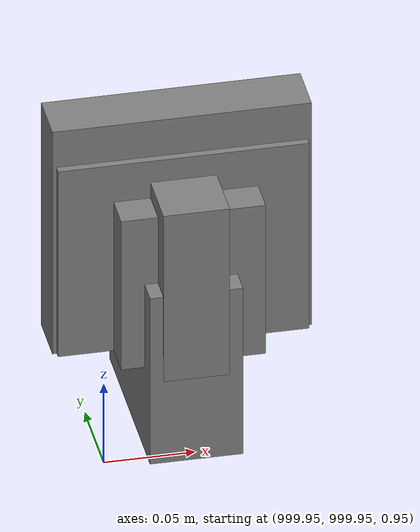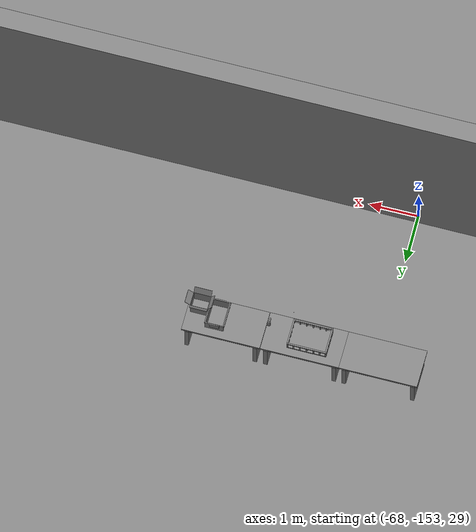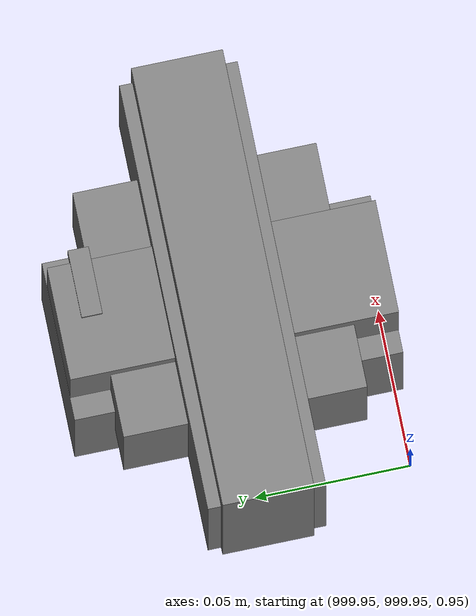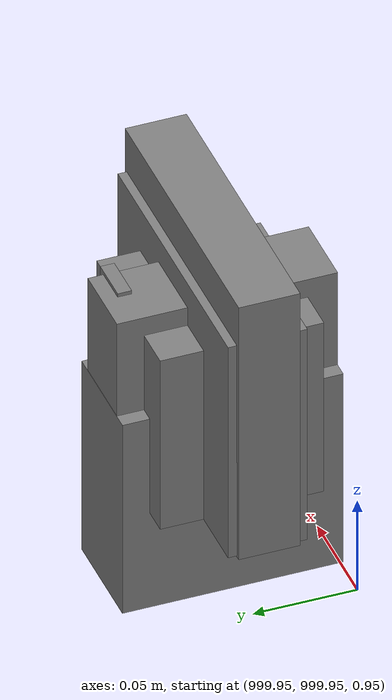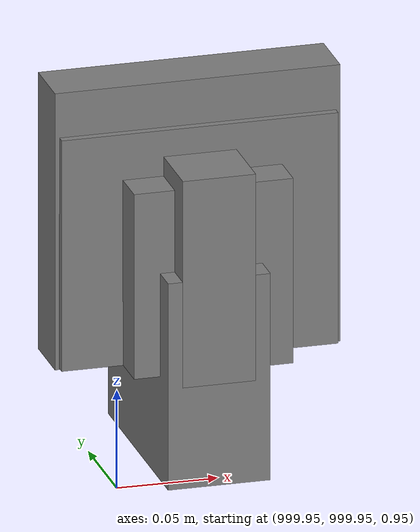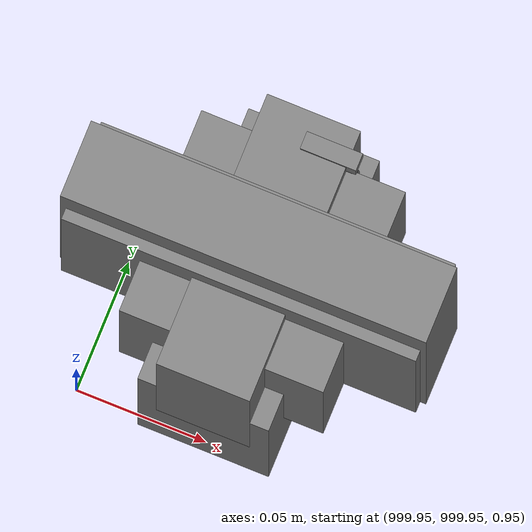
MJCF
<mujoco>
    <option gravity="0.000000000 0.000000000 -9.810000420" timestep="0.0049999999" integrator="implicitfast" density="1.225" viscosity="1.8000001e-05" noslip_iterations="10" iterations="100" sdf_iterations="50">
        <flag multiccd="disable"/>
    </option>
    <size memory="1000M"/>
    <compiler coordinate="local"/>
    <worldbody>
        <light cutoff="30" pos="0 1 1" dir="0 -1 -2"/>
        <light cutoff="30" pos="0 -1 1" dir="0 1 -2"/>
        <body pos="1000.000000000 1000.000000000 1.000000000" euler="0.000000000 0.000000000 180.000000000" name="openloong_gripper_2f85_fix_base_usda_battery_01">
            <geom contype="1" conaffinity="1" density="1000" type="box" material="" rgba="0.500000000 0.500000000 0.500000000 1.000000000" solimp="0.899999976 0.949999988 0.001000000" friction="1.000000000 0.005000000 0.000100000" solref="0.020000000 1.000000000" margin="0" condim="3" group="0" pos="-0.011123657 -0.041940309 0.101691343" quat="1.000000000 0.000000000 0.000000000 0.000000000" size="0.010800000 0.003375000 0.004725000" name="openloong_gripper_2f85_fix_base_usda_geom_50ADA970_E578_4D2D_B000_8B8C6AF99160"/>
            <geom contype="1" conaffinity="1" density="1000" type="box" material="" rgba="0.500000000 0.500000000 0.500000000 1.000000000" solimp="0.899999976 0.949999988 0.001000000" friction="1.000000000 0.005000000 0.000100000" solref="0.020000000 1.000000000" margin="0" condim="3" group="0" pos="-0.010876465 -0.044247437 0.047066893" quat="0.998702705 -0.050920475 0.000000000 0.000000000" size="0.009450001 0.002700000 0.024975000" name="openloong_gripper_2f85_fix_base_usda_geom_57949D55_28EA_4198_9B88_71555C056181"/>
            <geom contype="1" conaffinity="1" density="1000" type="box" material="" rgba="0.500000000 0.500000000 0.500000000 1.000000000" solimp="0.899999976 0.949999988 0.001000000" friction="1.000000000 0.005000000 0.000100000" solref="0.020000000 1.000000000" margin="0" condim="3" group="0" pos="-0.001235962 -0.000659180 0.047381196" quat="1.000000000 0.000000000 0.000000000 0.000000000" size="0.039420001 0.039150000 0.047250003" name="openloong_gripper_2f85_fix_base_usda_geom_20B99D6F_0FB3_48BB_8B8B_73678CC3B704"/>
            <geom contype="1" conaffinity="1" density="1000" type="box" material="" rgba="0.500000000 0.500000000 0.500000000 1.000000000" solimp="0.899999976 0.949999988 0.001000000" friction="1.000000000 0.005000000 0.000100000" solref="0.020000000 1.000000000" margin="0" condim="3" group="0" pos="-0.010876465 -0.039138794 0.009851727" quat="1.000000000 0.000000000 0.000000000 0.000000000" size="0.009450001 0.010800000 0.013500000" name="openloong_gripper_2f85_fix_base_usda_geom_3DFDB2A1_4690_4A83_8148_0FA73422A39B"/>
            <geom contype="1" conaffinity="1" density="1000" type="box" material="" rgba="0.500000000 0.500000000 0.500000000 1.000000000" solimp="0.899999976 0.949999988 0.001000000" friction="1.000000000 0.005000000 0.000100000" solref="0.020000000 1.000000000" margin="0" condim="3" group="0" pos="-0.010876465 -0.041528322 0.071508206" quat="1.000000000 0.000000000 0.000000000 0.000000000" size="0.009450001 0.002700000 0.027000001" name="openloong_gripper_2f85_fix_base_usda_geom_D262DE01_F28B_4E28_8170_038A02F85091"/>
            <freejoint name="openloong_gripper_2f85_fix_base_usda_battery_01_joint"/>
            <site size="0.005000000 0.005000000 0.005000000" rgba="0.500000000 0.500000000 0.500000000 1.000000000" pos="0.000000000 0.000000000 0.000000000" quat="0.999961913 0.008726500 0.000000000 0.000000000" group="0" type="sphere" name="openloong_gripper_2f85_fix_base_usda_battery_01site"/>
        </body>
        <body pos="-66.298110962 -149.564285278 31.168560028" euler="92.264274597 -53.023719788 149.173278809" mocap="true" name="spotlight3_SpotLight"/>
        <body pos="1000.000000000 1000.000000000 1.000000000" euler="0.000000000 0.000000000 180.000000000" name="openloong_gripper_2f85_fix_base_usda_cpu_fan">
            <geom contype="1" conaffinity="1" density="1000" type="box" material="" rgba="0.500000000 0.500000000 0.500000000 1.000000000" solimp="0.899999976 0.949999988 0.001000000" friction="1.000000000 0.005000000 0.000100000" solref="0.020000000 1.000000000" margin="0" condim="3" group="0" pos="0.000000000 0.000000000 0.070034981" quat="0.000000000 0.000000000 0.000000000 1.000000000" size="0.070700005 0.014699999 0.070700005" name="openloong_gripper_2f85_fix_base_usda_geom_C7470986_4C41_45FE_BA6F_2FB2CB3C6F1D"/>
            <freejoint name="openloong_gripper_2f85_fix_base_usda_cpu_fan_joint"/>
            <site size="0.005000000 0.005000000 0.005000000" rgba="0.500000000 0.500000000 0.500000000 1.000000000" pos="0.000000000 0.000000000 0.000000000" quat="0.999961913 0.008726535 0.000000000 0.000000000" group="0" type="sphere" name="openloong_gripper_2f85_fix_base_usda_cpu_fancsite"/>
        </body>
        <body pos="1000.000000000 1000.000000000 1.000000000" euler="0.000000000 0.000000000 180.000000000" name="openloong_gripper_2f85_fix_base_usda_wifi_box">
            <geom contype="1" conaffinity="1" density="1000" type="box" material="" rgba="0.500000000 0.500000000 0.500000000 1.000000000" solimp="0.899999976 0.949999988 0.001000000" friction="1.000000000 0.005000000 0.000100000" solref="0.020000000 1.000000000" margin="0" condim="3" group="0" pos="0.000000000 0.000000000 0.058978677" quat="0.000000000 0.000000047 0.000000000 1.000000000" size="0.068499997 0.018999999 0.059000000" name="openloong_gripper_2f85_fix_base_usda_geom_B79CF9AD_8BE3_4CEC_891C_F1310D10BD7E"/>
            <freejoint name="openloong_gripper_2f85_fix_base_usda_wifi_box_joint"/>
            <site size="0.005000000 0.005000000 0.005000000" rgba="0.500000000 0.500000000 0.500000000 1.000000000" pos="0.000000000 0.000000000 0.000000000" quat="0.999961913 0.008726500 0.000000000 0.000000000" group="0" type="sphere" name="openloong_gripper_2f85_fix_base_usda_wifi_boxsite"/>
        </body>
        <body pos="1000.000000000 1000.000000000 1.000000000" euler="0.000011953 0.000005123 -179.999984741" name="openloong_gripper_2f85_fix_base_usda_intel_box">
            <geom contype="1" conaffinity="1" density="1000" type="box" material="" rgba="0.500000000 0.500000000 0.500000000 1.000000000" solimp="0.899999976 0.949999988 0.001000000" friction="1.000000000 0.005000000 0.000100000" solref="0.020000000 1.000000000" margin="0" condim="3" group="0" pos="0.000000000 -0.000067139 0.000082284" quat="0.707106709 0.000000225 0.000000253 0.707106650" size="0.052800003 0.025300000 0.052800003" name="openloong_gripper_2f85_fix_base_usda_geom_4FA068E4_4C61_4C9E_AF68_F7F617927119"/>
            <freejoint name="openloong_gripper_2f85_fix_base_usda_intel_box_joint"/>
            <site size="0.005000000 0.005000000 0.005000000" rgba="0.500000000 0.500000000 0.500000000 1.000000000" pos="0.000000000 0.000000000 0.000000000" quat="0.999961913 0.008726500 0.000000000 0.000000000" group="0" type="sphere" name="openloong_gripper_2f85_fix_base_usda_intel_boxsite"/>
        </body>
        <body pos="-66.059059143 -149.355499268 31.165254593" euler="-34.120643616 -63.153114319 -123.783935547" mocap="true" name="spotlight5_SpotLight"/>
        <body pos="1000.000000000 999.999938965 1.000000000" euler="0.000000000 0.000000000 180.000000000" name="openloong_gripper_2f85_fix_base_usda_intelcore_i5">
            <geom contype="1" conaffinity="1" density="1000" type="box" material="" rgba="0.500000000 0.500000000 0.500000000 1.000000000" solimp="0.899999976 0.949999988 0.001000000" friction="1.000000000 0.005000000 0.000100000" solref="0.020000000 1.000000000" margin="0" condim="3" group="0" pos="0.000000000 0.000000000 0.051722717" quat="0.707106709 0.000000000 0.000000000 -0.707106769" size="0.052800000 0.018080002 0.052800000" name="openloong_gripper_2f85_fix_base_usda_geom_008C5281_FDE4_4F2D_88CF_AE0D17371AAB"/>
            <freejoint name="openloong_gripper_2f85_fix_base_usda_intelcore_i5_joint"/>
            <site size="0.005000000 0.005000000 0.005000000" rgba="0.500000000 0.500000000 0.500000000 1.000000000" pos="0.000000000 0.000000000 0.000000000" quat="0.999961913 0.008726534 0.000000000 0.000000000" group="0" type="sphere" name="openloong_gripper_2f85_fix_base_usda_intelcore_i5site"/>
        </body>
        <body pos="-66.044754028 -149.007766724 31.169891357" euler="8.513236046 -56.333885193 -118.253158569" mocap="true" name="spotlight2_SpotLight"/>
        <body pos="-64.866622925 -149.383972168 30.183746338" euler="89.999984741 89.999946594 0.000000000" name="openloong_gripper_2f85_fix_base_usda_bluebox_01">
            <geom contype="1" conaffinity="1" density="1000" type="box" material="" rgba="0.500000000 0.500000000 0.500000000 1.000000000" solimp="0.899999976 0.949999988 0.001000000" friction="1.000000000 0.005000000 0.000100000" solref="0.020000000 1.000000000" margin="0" condim="3" group="0" pos="0.276580811 0.187225342 0.000068665" quat="0.707106948 0.000077471 0.707106352 0.000077486" size="0.100000001 0.057999998 0.010000000" name="openloong_gripper_2f85_fix_base_usda_geom_39F2D368_78A3_49D7_8F44_024527DA7E45"/>
            <geom contype="1" conaffinity="1" density="1000" type="box" material="" rgba="0.500000000 0.500000000 0.500000000 1.000000000" solimp="0.899999976 0.949999988 0.001000000" friction="1.000000000 0.005000000 0.000100000" solref="0.020000000 1.000000000" margin="0" condim="3" group="0" pos="0.000000000 0.002883911 0.000000000" quat="0.999999881 0.000000000 0.000000000 0.000000000" size="0.254000008 0.003000000 0.172000006" name="openloong_gripper_2f85_fix_base_usda_geom_0048C89E_B408_4423_AA94_9BE62544C1C1"/>
            <geom contype="1" conaffinity="1" density="1000" type="box" material="" rgba="0.500000000 0.500000000 0.500000000 1.000000000" solimp="0.899999976 0.949999988 0.001000000" friction="1.000000000 0.005000000 0.000100000" solref="0.020000000 1.000000000" margin="0" condim="3" group="0" pos="0.000000000 0.124874115 0.173484802" quat="0.999796331 0.020176515 -0.000000015 0.000000030" size="0.259999990 0.119999997 0.007000000" name="openloong_gripper_2f85_fix_base_usda_geom_DC575CB4_7AF9_46A8_B6C5_0CB9647DA523"/>
            <geom contype="1" conaffinity="1" density="1000" type="box" material="" rgba="0.500000000 0.500000000 0.500000000 1.000000000" solimp="0.899999976 0.949999988 0.001000000" friction="1.000000000 0.005000000 0.000100000" solref="0.020000000 1.000000000" margin="0" condim="3" group="0" pos="0.000000000 0.124874115 -0.173469543" quat="0.999796331 -0.020176545 -0.000000015 0.000000000" size="0.259999990 0.119999997 0.007000000" name="openloong_gripper_2f85_fix_base_usda_geom_BE2AAF8C_193B_4E3D_9995_93F4127C660E"/>
            <geom contype="1" conaffinity="1" density="1000" type="box" material="" rgba="0.500000000 0.500000000 0.500000000 1.000000000" solimp="0.899999976 0.949999988 0.001000000" friction="1.000000000 0.005000000 0.000100000" solref="0.020000000 1.000000000" margin="0" condim="3" group="0" pos="0.000000000 0.214008331 0.188980103" quat="0.999912977 0.013176724 0.000000015 0.000000000" size="0.259999990 0.029999999 0.012500000" name="openloong_gripper_2f85_fix_base_usda_geom_ECE03C1E_6C51_42E2_A8DF_BB1A0B6D4BA7"/>
            <geom contype="1" conaffinity="1" density="1000" type="box" material="" rgba="0.500000000 0.500000000 0.500000000 1.000000000" solimp="0.899999976 0.949999988 0.001000000" friction="1.000000000 0.005000000 0.000100000" solref="0.020000000 1.000000000" margin="0" condim="3" group="0" pos="-0.258361816 0.125289917 0.001876831" quat="0.702796936 -0.020792112 0.710783124 0.020769298" size="0.189999998 0.119999997 0.009000000" name="openloong_gripper_2f85_fix_base_usda_geom_16A62A1F_95E3_4172_B21E_91B8D9DB3913"/>
            <geom contype="1" conaffinity="1" density="1000" type="box" material="" rgba="0.500000000 0.500000000 0.500000000 1.000000000" solimp="0.899999976 0.949999988 0.001000000" friction="1.000000000 0.005000000 0.000100000" solref="0.020000000 1.000000000" margin="0" condim="3" group="0" pos="0.000000000 0.214008331 -0.188980103" quat="0.999912977 -0.013176769 0.000000030 0.000000015" size="0.259999990 0.029999999 0.012500000" name="openloong_gripper_2f85_fix_base_usda_geom_06929DDB_EFDA_4505_8EEB_A246DEB9C892"/>
            <geom contype="1" conaffinity="1" density="1000" type="box" material="" rgba="0.500000000 0.500000000 0.500000000 1.000000000" solimp="0.899999976 0.949999988 0.001000000" friction="1.000000000 0.005000000 0.000100000" solref="0.020000000 1.000000000" margin="0" condim="3" group="0" pos="-0.276611328 0.187225342 0.000068665" quat="0.707106650 0.000077441 0.707106709 0.000077456" size="0.100000001 0.057999998 0.010000000" name="openloong_gripper_2f85_fix_base_usda_geom_3A46CE0B_5F39_49A6_A2BA_7F10A91CE01D"/>
            <geom contype="1" conaffinity="1" density="1000" type="box" material="" rgba="0.500000000 0.500000000 0.500000000 1.000000000" solimp="0.899999976 0.949999988 0.001000000" friction="1.000000000 0.005000000 0.000100000" solref="0.020000000 1.000000000" margin="0" condim="3" group="0" pos="0.258331299 0.125289917 0.001876831" quat="0.702851415 0.018856421 0.710823774 -0.019329369" size="0.189999998 0.119999997 0.009000000" name="openloong_gripper_2f85_fix_base_usda_geom_E00D9818_221F_44F1_AC5D_E65D5B1F2756"/>
            <freejoint name="openloong_gripper_2f85_fix_base_usda_bluebox_01_joint"/>
            <site size="0.005000000 0.005000000 0.005000000" rgba="0.500000000 0.500000000 0.500000000 1.000000000" pos="0.000000000 0.000000000 0.000000000" quat="0.999961913 0.008726534 0.000000000 0.000000000" group="0" type="sphere" name="openloong_gripper_2f85_fix_base_usda_bluebox_01site"/>
        </body>
        <body pos="-64.496299744 -149.491867065 30.235729218" euler="0.000000000 0.000000000 89.999946594" name="openloong_gripper_2f85_fix_base_usda_cardboardbox_01">
            <geom contype="1" conaffinity="1" density="1000" type="box" material="" rgba="0.500000000 0.500000000 0.500000000 1.000000000" solimp="0.899999976 0.949999988 0.001000000" friction="1.000000000 0.005000000 0.000100000" solref="0.020000000 1.000000000" margin="0" condim="3" group="0" pos="-0.003166199 -0.004086494 0.005052090" quat="1.000000000 0.000000000 0.000000000 0.000000000" size="0.142499998 0.177500010 0.005000000" name="openloong_gripper_2f85_fix_base_usda_geom_2F386E8A_002C_4265_81C2_9E45CD8C3109"/>
            <geom contype="1" conaffinity="1" density="1000" type="box" material="" rgba="0.500000000 0.500000000 0.500000000 1.000000000" solimp="0.899999976 0.949999988 0.001000000" friction="1.000000000 0.005000000 0.000100000" solref="0.020000000 1.000000000" margin="0" condim="3" group="0" pos="-0.003166199 0.170316696 0.150570869" quat="1.000000000 0.000000000 0.000000000 0.000000000" size="0.142499998 0.005000000 0.149999991" name="openloong_gripper_2f85_fix_base_usda_geom_AC43B02B_5152_4CA3_BE43_460A56E04833"/>
            <geom contype="1" conaffinity="1" density="1000" type="box" material="" rgba="0.500000000 0.500000000 0.500000000 1.000000000" solimp="0.899999976 0.949999988 0.001000000" friction="1.000000000 0.005000000 0.000100000" solref="0.020000000 1.000000000" margin="0" condim="3" group="0" pos="-0.147399902 -0.005307198 0.150570869" quat="1.000000000 0.000000000 0.000000000 0.000000000" size="0.005000000 0.177500010 0.149999991" name="openloong_gripper_2f85_fix_base_usda_geom_314E4B15_2FBE_41F9_A574_12C13454C455"/>
            <geom contype="1" conaffinity="1" density="1000" type="box" material="" rgba="0.500000000 0.500000000 0.500000000 1.000000000" solimp="0.899999976 0.949999988 0.001000000" friction="1.000000000 0.005000000 0.000100000" solref="0.020000000 1.000000000" margin="0" condim="3" group="0" pos="0.140275955 -0.005307198 0.150570869" quat="1.000000000 0.000000000 0.000000000 0.000000000" size="0.005000000 0.177500010 0.149999991" name="openloong_gripper_2f85_fix_base_usda_geom_A472B560_D127_43E9_B72F_C43F17558E41"/>
            <geom contype="1" conaffinity="1" density="1000" type="box" material="" rgba="0.500000000 0.500000000 0.500000000 1.000000000" solimp="0.899999976 0.949999988 0.001000000" friction="1.000000000 0.005000000 0.000100000" solref="0.020000000 1.000000000" margin="0" condim="3" group="0" pos="-0.003166199 -0.181550980 0.150570869" quat="1.000000000 0.000000000 0.000000000 0.000000000" size="0.142499998 0.005000000 0.149999991" name="openloong_gripper_2f85_fix_base_usda_geom_BC1C55D1_55C5_4652_83B6_5D5660FB9254"/>
            <freejoint name="openloong_gripper_2f85_fix_base_usda_cardboardbox_01_joint"/>
            <site size="0.005000000 0.005000000 0.005000000" rgba="0.500000000 0.500000000 0.500000000 1.000000000" pos="0.000000000 0.000000000 0.000000000" quat="0.999961913 0.008726535 0.000000000 0.000000000" group="0" type="sphere" name="openloong_gripper_2f85_fix_base_usda_site_7E649AD7_BCB4_4A64_8CEA_6BF2916A7F80"/>
            <body pos="0.139160156 -0.004048347 0.301930904" euler="-179.999954224 49.383502960 179.999954224" name="openloong_gripper_2f85_fix_base_usda_A1_006">
                <geom contype="1" conaffinity="1" density="1000" type="box" material="" rgba="0.500000000 0.500000000 0.500000000 1.000000000" solimp="0.899999976 0.949999988 0.001000000" friction="1.000000000 0.005000000 0.000100000" solref="0.020000000 1.000000000" margin="0" condim="3" group="0" pos="-0.071587563 0.000009537 0.001745224" quat="0.999999881 0.000000000 0.000000000 0.000000000" size="0.071249999 0.179999992 0.002500000" name="openloong_gripper_2f85_fix_base_usda_geom_16BB55DB_C166_4040_9499_836D4B7BD78A"/>
                <joint armature="0" stiffness="0.07" damping="0.0099999998" axis="0.000000 1.000000 0.000000" type="hinge" name="openloong_gripper_2f85_fix_base_usda_A1_006"/>
            </body>
            <body pos="-0.145902634 -0.004086494 0.301938057" euler="-180.000000000 -60.000011444 -180.000000000" name="openloong_gripper_2f85_fix_base_usda_A2_006">
                <geom contype="1" conaffinity="1" density="1000" type="box" material="" rgba="0.500000000 0.500000000 0.500000000 1.000000000" solimp="0.899999976 0.949999988 0.001000000" friction="1.000000000 0.005000000 0.000100000" solref="0.020000000 1.000000000" margin="0" condim="3" group="0" pos="0.071268082 0.000009537 0.002717972" quat="0.000002921 0.000000000 -0.000000030 0.999999881" size="0.071249999 0.179999992 0.002500000" name="openloong_gripper_2f85_fix_base_usda_geom_1365DEC3_A836_41A3_B600_DD7FE4529E6B"/>
                <joint armature="0" stiffness="0.07" damping="0.0099999998" axis="0.000000 1.000000 0.000000" type="hinge" name="openloong_gripper_2f85_fix_base_usda_A2_006"/>
            </body>
            <body pos="-0.003385544 0.175991058 0.301930904" euler="-125.858116150 -0.000004561 0.000002331" name="openloong_gripper_2f85_fix_base_usda_B2_006">
                <geom contype="1" conaffinity="1" density="1000" type="box" material="" rgba="0.500000000 0.500000000 0.500000000 1.000000000" solimp="0.899999976 0.949999988 0.001000000" friction="1.000000000 0.005000000 0.000100000" solref="0.020000000 1.000000000" margin="0" condim="3" group="0" pos="0.000009537 -0.070939064 -0.002470016" quat="0.999614120 0.027776197 -0.000000015 0.000000030" size="0.137500003 0.064999998 0.005000000" name="openloong_gripper_2f85_fix_base_usda_geom_B44CEB2E_03BC_4E9F_83C5_935D0E152764"/>
                <joint armature="0" stiffness="0.07" damping="0.0099999998" axis="1.000000 0.000000 0.000000" type="hinge" name="openloong_gripper_2f85_fix_base_usda_B2_006"/>
            </body>
            <body pos="-0.003385544 -0.184140205 0.301938057" euler="147.805557251 0.000000000 0.000000000" name="openloong_gripper_2f85_fix_base_usda_B1_006">
                <geom contype="1" conaffinity="1" density="1000" type="box" material="" rgba="0.500000000 0.500000000 0.500000000 1.000000000" solimp="0.899999976 0.949999988 0.001000000" friction="1.000000000 0.005000000 0.000100000" solref="0.020000000 1.000000000" margin="0" condim="3" group="0" pos="-0.000028610 0.070202351 -0.002703667" quat="0.999614179 -0.027776167 0.000000000 0.000000000" size="0.137500003 0.064999998 0.005000000" name="openloong_gripper_2f85_fix_base_usda_geom_D8551840_CB14_486B_8B08_75BDCBC36EC0"/>
                <joint armature="0" stiffness="0.07" damping="0.0099999998" axis="1.000000 0.000000 0.000000" type="hinge" name="openloong_gripper_2f85_fix_base_usda_B1_006"/>
            </body>
        </body>
        <body pos="-65.882858276 -149.481979370 30.229999542" euler="-64.487716675 0.000000000 0.000000000" name="openloong_gripper_2f85_fix_base_usda_Barcode">
            <geom contype="1" conaffinity="1" density="1000" type="box" material="" rgba="0.500000000 0.500000000 0.500000000 1.000000000" solimp="0.899999976 0.949999988 0.001000000" friction="1.000000000 0.005000000 0.000100000" solref="0.020000000 1.000000000" margin="0" condim="3" group="0" pos="0.000000000 0.013038635 0.001419067" quat="0.000000000 0.000000000 0.000000000 1.000000119" size="0.034000002 0.010000000 0.017999999" name="openloong_gripper_2f85_fix_base_usda_geom_F16C7E33_0DA4_4008_86EA_30A5A3372AA2"/>
            <geom contype="1" conaffinity="1" density="1000" type="box" material="" rgba="0.500000000 0.500000000 0.500000000 1.000000000" solimp="0.899999976 0.949999988 0.001000000" friction="1.000000000 0.005000000 0.000100000" solref="0.020000000 1.000000000" margin="0" condim="3" group="0" pos="0.000000000 -0.035301208 -0.007095337" quat="0.000000000 0.000000000 -0.043619365 0.999048233" size="0.028999999 0.010000000 0.020000000" name="openloong_gripper_2f85_fix_base_usda_geom_5731DD3C_4017_411B_95E1_ED768279230C"/>
            <geom contype="1" conaffinity="1" density="1000" type="box" material="" rgba="0.500000000 0.500000000 0.500000000 1.000000000" solimp="0.899999976 0.949999988 0.001000000" friction="1.000000000 0.005000000 0.000100000" solref="0.020000000 1.000000000" margin="0" condim="3" group="0" pos="0.000000000 -0.043411255 -0.011749268" quat="0.922262907 0.386563420 0.000000000 0.000000000" size="0.026000001 0.010000000 0.020000000" name="openloong_gripper_2f85_fix_base_usda_geom_D0D9CA8A_330D_4024_9B41_49BD26DB4CCE"/>
            <geom contype="1" conaffinity="1" density="1000" type="box" material="" rgba="0.500000000 0.500000000 0.500000000 1.000000000" solimp="0.899999976 0.949999988 0.001000000" friction="1.000000000 0.005000000 0.000100000" solref="0.020000000 1.000000000" margin="0" condim="3" group="0" pos="0.000000000 -0.016967773 -0.031860352" quat="0.000000000 0.000000000 0.000000000 1.000000119" size="0.008000000 0.010000000 0.013000000" name="openloong_gripper_2f85_fix_base_usda_geom_29DF8ACF_497A_412E_8E5A_4654C4AAFDC9"/>
            <geom contype="1" conaffinity="1" density="1000" type="box" material="" rgba="0.500000000 0.500000000 0.500000000 1.000000000" solimp="0.899999976 0.949999988 0.001000000" friction="1.000000000 0.005000000 0.000100000" solref="0.020000000 1.000000000" margin="0" condim="3" group="0" pos="0.000000000 -0.001869202 0.000312805" quat="0.953716993 0.300705761 0.000000000 0.000000000" size="0.032000002 0.010000000 0.018999999" name="openloong_gripper_2f85_fix_base_usda_geom_53AF21EA_EAC0_471E_BECC_2C23A12A0C7E"/>
            <geom contype="1" conaffinity="1" density="1000" type="box" material="" rgba="0.500000000 0.500000000 0.500000000 1.000000000" solimp="0.899999976 0.949999988 0.001000000" friction="1.000000000 0.005000000 0.000100000" solref="0.020000000 1.000000000" margin="0" condim="3" group="0" pos="0.000000000 -0.019531250 -0.003173828" quat="0.953716993 0.300705761 0.000000000 0.000000000" size="0.030999999 0.010000000 0.020000000" name="openloong_gripper_2f85_fix_base_usda_geom_2732B079_9124_4343_8999_EBEA7679174D"/>
            <geom contype="1" conaffinity="1" density="1000" type="box" material="" rgba="0.500000000 0.500000000 0.500000000 1.000000000" solimp="0.899999976 0.949999988 0.001000000" friction="1.000000000 0.005000000 0.000100000" solref="0.020000000 1.000000000" margin="0" condim="3" group="0" pos="0.000000000 -0.035301208 -0.007095337" quat="0.953716993 0.300705761 0.000000000 0.000000000" size="0.028999999 0.010000000 0.020000000" name="openloong_gripper_2f85_fix_base_usda_geom_F8D392E5_DAF9_4075_9055_25B2B9D213F0"/>
            <geom contype="1" conaffinity="1" density="1000" type="box" material="" rgba="0.500000000 0.500000000 0.500000000 1.000000000" solimp="0.899999976 0.949999988 0.001000000" friction="1.000000000 0.005000000 0.000100000" solref="0.020000000 1.000000000" margin="0" condim="3" group="0" pos="0.000000000 -0.042617798 -0.071121216" quat="0.000000000 0.000000000 0.000000000 1.000000119" size="0.013000000 0.021000000 0.059999999" name="openloong_gripper_2f85_fix_base_usda_geom_F5DF0D1B_C850_40A9_A169_1970B09A68F1"/>
            <freejoint name="openloong_gripper_2f85_fix_base_usda_Barcode_joint"/>
            <site size="0.005000000 0.005000000 0.005000000" rgba="0.500000000 0.500000000 0.500000000 1.000000000" pos="0.000000000 0.000000000 0.000000000" quat="1.000000000 0.000000000 0.000000000 0.000000000" group="0" type="sphere" name="openloong_gripper_2f85_fix_base_usda_Barcode_site"/>
        </body>
        <body pos="-66.745018005 -149.392349243 30.184000015" euler="0.000000000 0.000000000 89.999946594" name="[22332682064712]_Basket_01">
            <geom contype="1" conaffinity="1" density="1000" type="box" material="" rgba="0.500000000 0.500000000 0.500000000 1.000000000" solimp="0.899999976 0.949999988 0.001000000" friction="1.000000000 0.005000000 0.000100000" solref="0.020000000 1.000000000" margin="0" condim="3" group="0" pos="-0.052425385 0.389207840 0.089787483" quat="0.707107008 0.000000000 0.000000000 0.707106411" size="0.014249999 0.014249999 0.059999999" name="[22332682064712]_geom_1F9CEAE3_39A6_4126_8520_BD10E4672008"/>
            <geom contype="1" conaffinity="1" density="1000" type="box" material="" rgba="0.500000000 0.500000000 0.500000000 1.000000000" solimp="0.899999976 0.949999988 0.001000000" friction="1.000000000 0.005000000 0.000100000" solref="0.020000000 1.000000000" margin="0" condim="3" group="0" pos="0.264015198 -0.133043289 0.089787483" quat="0.707107008 0.000000000 0.000000000 0.707106411" size="0.014249999 0.014249999 0.059999999" name="[22332682064712]_geom_C2295B33_583F_48F5_8754_FC061935726E"/>
            <geom contype="1" conaffinity="1" density="1000" type="box" material="" rgba="0.500000000 0.500000000 0.500000000 1.000000000" solimp="0.899999976 0.949999988 0.001000000" friction="1.000000000 0.005000000 0.000100000" solref="0.020000000 1.000000000" margin="0" condim="3" group="0" pos="-0.264015198 -0.265548706 0.089793205" quat="0.707107008 0.000000000 0.000000000 0.707106411" size="0.014249999 0.014249999 0.059999999" name="[22332682064712]_geom_090974C0_6F04_4721_964E_75C1686561D9"/>
            <geom contype="1" conaffinity="1" density="1000" type="box" material="" rgba="0.500000000 0.500000000 0.500000000 1.000000000" solimp="0.899999976 0.949999988 0.001000000" friction="1.000000000 0.005000000 0.000100000" solref="0.020000000 1.000000000" margin="0" condim="3" group="0" pos="-0.160263062 -0.389322281 0.089793205" quat="0.707107008 0.000000000 0.000000000 0.707106411" size="0.014249999 0.014249999 0.059999999" name="[22332682064712]_geom_CDDB3B5E_5DE2_4BB7_898B_70C46D89F327"/>
            <geom contype="1" conaffinity="1" density="1000" type="box" material="" rgba="0.500000000 0.500000000 0.500000000 1.000000000" solimp="0.899999976 0.949999988 0.001000000" friction="1.000000000 0.005000000 0.000100000" solref="0.020000000 1.000000000" margin="0" condim="3" group="0" pos="0.162265778 -0.389322281 0.089787483" quat="0.707107008 0.000000000 0.000000000 0.707106411" size="0.014249999 0.014249999 0.059999999" name="[22332682064712]_geom_5D2B2F97_B890_49FA_AD49_848E3C99222F"/>
            <geom contype="1" conaffinity="1" density="1000" type="box" material="" rgba="0.500000000 0.500000000 0.500000000 1.000000000" solimp="0.899999976 0.949999988 0.001000000" friction="1.000000000 0.005000000 0.000100000" solref="0.020000000 1.000000000" margin="0" condim="3" group="0" pos="0.264015198 0.389207840 0.089787483" quat="0.707107008 0.000000000 0.000000000 0.707106411" size="0.014249999 0.014249999 0.059999999" name="[22332682064712]_geom_6301EEB7_C3F8_44F2_B067_A60E770E8758"/>
            <geom contype="1" conaffinity="1" density="1000" type="box" material="" rgba="0.500000000 0.500000000 0.500000000 1.000000000" solimp="0.899999976 0.949999988 0.001000000" friction="1.000000000 0.005000000 0.000100000" solref="0.020000000 1.000000000" margin="0" condim="3" group="0" pos="-0.264015198 -0.133043289 0.089793205" quat="0.707107008 0.000000000 0.000000000 0.707106411" size="0.014249999 0.014249999 0.059999999" name="[22332682064712]_geom_21CB9FBE_F031_4D82_9464_29ECFD8BBB4C"/>
            <geom contype="1" conaffinity="1" density="1000" type="box" material="" rgba="0.500000000 0.500000000 0.500000000 1.000000000" solimp="0.899999976 0.949999988 0.001000000" friction="1.000000000 0.005000000 0.000100000" solref="0.020000000 1.000000000" margin="0" condim="3" group="0" pos="-0.264026642 0.269256592 0.089793205" quat="0.707107008 0.000000000 0.000000000 0.707106411" size="0.014249999 0.014249999 0.059999999" name="[22332682064712]_geom_899699BA_98A4_4593_9FC1_F0F312852CED"/>
            <geom contype="1" conaffinity="1" density="1000" type="box" material="" rgba="0.500000000 0.500000000 0.500000000 1.000000000" solimp="0.899999976 0.949999988 0.001000000" friction="1.000000000 0.005000000 0.000100000" solref="0.020000000 1.000000000" margin="0" condim="3" group="0" pos="0.054462433 0.389207840 0.089787483" quat="0.707107008 0.000000000 0.000000000 0.707106411" size="0.014249999 0.014249999 0.059999999" name="[22332682064712]_geom_DF4EE184_A482_44F4_9B0F_A0D3CB53AE25"/>
            <geom contype="1" conaffinity="1" density="1000" type="box" material="" rgba="0.500000000 0.500000000 0.500000000 1.000000000" solimp="0.899999976 0.949999988 0.001000000" friction="1.000000000 0.005000000 0.000100000" solref="0.020000000 1.000000000" margin="0" condim="3" group="0" pos="0.054462433 -0.389322281 0.089787483" quat="0.707107008 0.000000000 0.000000000 0.707106411" size="0.014249999 0.014249999 0.059999999" name="[22332682064712]_geom_21C8B464_E937_47AC_B353_3B05D66C5443"/>
            <geom contype="1" conaffinity="1" density="1000" type="box" material="" rgba="0.500000000 0.500000000 0.500000000 1.000000000" solimp="0.899999976 0.949999988 0.001000000" friction="1.000000000 0.005000000 0.000100000" solref="0.020000000 1.000000000" margin="0" condim="3" group="0" pos="0.264015198 0.269256592 0.089793205" quat="0.707107008 0.000000000 0.000000000 0.707106411" size="0.014249999 0.014249999 0.059999999" name="[22332682064712]_geom_263E4CA8_371F_4FEA_AB42_26A2C5AB5776"/>
            <geom contype="1" conaffinity="1" density="1000" type="box" material="" rgba="0.500000000 0.500000000 0.500000000 1.000000000" solimp="0.899999976 0.949999988 0.001000000" friction="1.000000000 0.005000000 0.000100000" solref="0.020000000 1.000000000" margin="0" condim="3" group="0" pos="0.264015198 -0.389322281 0.089787483" quat="0.707107008 0.000000000 0.000000000 0.707106411" size="0.014249999 0.014249999 0.059999999" name="[22332682064712]_geom_3EED607A_6D05_4A37_9EDB_A824AF13BE19"/>
            <geom contype="1" conaffinity="1" density="1000" type="box" material="" rgba="0.500000000 0.500000000 0.500000000 1.000000000" solimp="0.899999976 0.949999988 0.001000000" friction="1.000000000 0.005000000 0.000100000" solref="0.020000000 1.000000000" margin="0" condim="3" group="0" pos="0.000000000 0.000000000 0.015998840" quat="0.707107008 0.000000000 0.000000000 0.707106411" size="0.403499991 0.279000014 0.015750000" name="[22332682064712]_geom_AE133264_0B76_465D_8EFD_AF860FAA4C1C"/>
            <geom contype="1" conaffinity="1" density="1000" type="box" material="" rgba="0.500000000 0.500000000 0.500000000 1.000000000" solimp="0.899999976 0.949999988 0.001000000" friction="1.000000000 0.005000000 0.000100000" solref="0.020000000 1.000000000" margin="0" condim="3" group="0" pos="0.000000000 -0.389476776 0.163619041" quat="0.707107008 0.000000000 0.000000000 0.707106411" size="0.015000000 0.277500004 0.015750000" name="[22332682064712]_geom_A1BFE779_E8EE_4062_B5F5_206B9B96EDA8"/>
            <geom contype="1" conaffinity="1" density="1000" type="box" material="" rgba="0.500000000 0.500000000 0.500000000 1.000000000" solimp="0.899999976 0.949999988 0.001000000" friction="1.000000000 0.005000000 0.000100000" solref="0.020000000 1.000000000" margin="0" condim="3" group="0" pos="0.162265778 0.389207840 0.089787483" quat="0.707107008 0.000000000 0.000000000 0.707106411" size="0.014249999 0.014249999 0.059999999" name="[22332682064712]_geom_257E6ADA_26F7_4663_A87F_A4F845EBC9BD"/>
            <geom contype="1" conaffinity="1" density="1000" type="box" material="" rgba="0.500000000 0.500000000 0.500000000 1.000000000" solimp="0.899999976 0.949999988 0.001000000" friction="1.000000000 0.005000000 0.000100000" solref="0.020000000 1.000000000" margin="0" condim="3" group="0" pos="0.000000000 0.389471054 0.163619041" quat="0.707107008 0.000000000 0.000000000 0.707106411" size="0.015000000 0.277500004 0.015750000" name="[22332682064712]_geom_C5D50B37_89B7_44CC_9A8C_280D50BEB353"/>
            <geom contype="1" conaffinity="1" density="1000" type="box" material="" rgba="0.500000000 0.500000000 0.500000000 1.000000000" solimp="0.899999976 0.949999988 0.001000000" friction="1.000000000 0.005000000 0.000100000" solref="0.020000000 1.000000000" margin="0" condim="3" group="0" pos="-0.263511658 0.000000000 0.163619041" quat="0.707107008 0.000000000 0.000000000 0.707106411" size="0.403499991 0.015000000 0.015750000" name="[22332682064712]_geom_67E94389_E209_4CEC_8E82_6036D65DC347"/>
            <geom contype="1" conaffinity="1" density="1000" type="box" material="" rgba="0.500000000 0.500000000 0.500000000 1.000000000" solimp="0.899999976 0.949999988 0.001000000" friction="1.000000000 0.005000000 0.000100000" solref="0.020000000 1.000000000" margin="0" condim="3" group="0" pos="-0.264015198 0.141334534 0.089793205" quat="0.707107008 0.000000000 0.000000000 0.707106411" size="0.014249999 0.014249999 0.059999999" name="[22332682064712]_geom_5CE7FFDC_2D17_450C_9FAF_361F21424FAF"/>
            <geom contype="1" conaffinity="1" density="1000" type="box" material="" rgba="0.500000000 0.500000000 0.500000000 1.000000000" solimp="0.899999976 0.949999988 0.001000000" friction="1.000000000 0.005000000 0.000100000" solref="0.020000000 1.000000000" margin="0" condim="3" group="0" pos="0.264015198 -0.265548706 0.089787483" quat="0.707107008 0.000000000 0.000000000 0.707106411" size="0.014249999 0.014249999 0.059999999" name="[22332682064712]_geom_CBDA8058_D1EB_4713_AA81_5B340E11F478"/>
            <geom contype="1" conaffinity="1" density="1000" type="box" material="" rgba="0.500000000 0.500000000 0.500000000 1.000000000" solimp="0.899999976 0.949999988 0.001000000" friction="1.000000000 0.005000000 0.000100000" solref="0.020000000 1.000000000" margin="0" condim="3" group="0" pos="-0.160263062 0.389207840 0.089787483" quat="0.707107008 0.000000000 0.000000000 0.707106411" size="0.014249999 0.014249999 0.059999999" name="[22332682064712]_geom_3D94A518_F865_4E2C_938B_D1D3A374A055"/>
            <geom contype="1" conaffinity="1" density="1000" type="box" material="" rgba="0.500000000 0.500000000 0.500000000 1.000000000" solimp="0.899999976 0.949999988 0.001000000" friction="1.000000000 0.005000000 0.000100000" solref="0.020000000 1.000000000" margin="0" condim="3" group="0" pos="-0.052425385 -0.389322281 0.089787483" quat="0.707107008 0.000000000 0.000000000 0.707106411" size="0.014249999 0.014249999 0.059999999" name="[22332682064712]_geom_36404285_F27F_40B9_833A_06FAFA63FAE3"/>
            <geom contype="1" conaffinity="1" density="1000" type="box" material="" rgba="0.500000000 0.500000000 0.500000000 1.000000000" solimp="0.899999976 0.949999988 0.001000000" friction="1.000000000 0.005000000 0.000100000" solref="0.020000000 1.000000000" margin="0" condim="3" group="0" pos="-0.264026642 -0.389322281 0.089793205" quat="0.707107008 0.000000000 0.000000000 0.707106411" size="0.014249999 0.014249999 0.059999999" name="[22332682064712]_geom_ED04859B_C5F4_4681_85E9_9C74F941A414"/>
            <geom contype="1" conaffinity="1" density="1000" type="box" material="" rgba="0.500000000 0.500000000 0.500000000 1.000000000" solimp="0.899999976 0.949999988 0.001000000" friction="1.000000000 0.005000000 0.000100000" solref="0.020000000 1.000000000" margin="0" condim="3" group="0" pos="0.264015198 0.141334534 0.089787483" quat="0.707107008 0.000000000 0.000000000 0.707106411" size="0.014249999 0.014249999 0.059999999" name="[22332682064712]_geom_5F063945_8EFE_440F_AE7B_50429C25BF9B"/>
            <geom contype="1" conaffinity="1" density="1000" type="box" material="" rgba="0.500000000 0.500000000 0.500000000 1.000000000" solimp="0.899999976 0.949999988 0.001000000" friction="1.000000000 0.005000000 0.000100000" solref="0.020000000 1.000000000" margin="0" condim="3" group="0" pos="-0.264015198 0.389207840 0.089793205" quat="0.707107008 0.000000000 0.000000000 0.707106411" size="0.014249999 0.014249999 0.059999999" name="[22332682064712]_geom_700F69F9_76A4_4E81_91C8_57ECB38A0463"/>
            <geom contype="1" conaffinity="1" density="1000" type="box" material="" rgba="0.500000000 0.500000000 0.500000000 1.000000000" solimp="0.899999976 0.949999988 0.001000000" friction="1.000000000 0.005000000 0.000100000" solref="0.020000000 1.000000000" margin="0" condim="3" group="0" pos="0.264015198 0.004480362 0.089787483" quat="0.707107008 0.000000000 0.000000000 0.707106411" size="0.014249999 0.014249999 0.059999999" name="[22332682064712]_geom_B0A138F2_DA58_4E9A_AA71_EE0421C7091B"/>
            <geom contype="1" conaffinity="1" density="1000" type="box" material="" rgba="0.500000000 0.500000000 0.500000000 1.000000000" solimp="0.899999976 0.949999988 0.001000000" friction="1.000000000 0.005000000 0.000100000" solref="0.020000000 1.000000000" margin="0" condim="3" group="0" pos="0.263694763 -0.000011444 0.163619041" quat="0.707107008 0.000000000 0.000000000 0.707106411" size="0.403499991 0.015000000 0.015750000" name="[22332682064712]_geom_B1E3A92C_AAF0_4E3D_B994_3B2857777D04"/>
            <geom contype="1" conaffinity="1" density="1000" type="box" material="" rgba="0.500000000 0.500000000 0.500000000 1.000000000" solimp="0.899999976 0.949999988 0.001000000" friction="1.000000000 0.005000000 0.000100000" solref="0.020000000 1.000000000" margin="0" condim="3" group="0" pos="-0.264015198 0.004480362 0.089793205" quat="0.707107008 0.000000000 0.000000000 0.707106411" size="0.014249999 0.014249999 0.059999999" name="[22332682064712]_geom_9AE50663_4582_40E1_876D_F26BB247893C"/>
            <freejoint name="[22332682064712]_joint_4A4839DA_2BB9_4085_8EA9_00137698F09F"/>
        </body>
        <body pos="0.000000000 0.000000000 0.000000000" euler="0.000000000 0.000000000 0.000000000" name="Static Objects_Static Objects">
            <geom contype="1" conaffinity="1" density="1000" type="box" material="" rgba="0.500000000 0.500000000 0.500000000 1.000000000" solimp="0.899999976 0.949999988 0.001000000" friction="1.000000000 0.005000000 0.000100000" solref="0.020000000 1.000000000" margin="0" condim="3" group="0" pos="-67.544113159 -149.365814209 29.727830887" quat="0.500000417 0.499999970 0.499999553 0.499999970" size="0.381000012 0.319999993 0.041000001" name="Static Objects_geom_CEEEF5F4_5728_4204_8C46_02ECE73E8A4B"/>
            <geom contype="1" conaffinity="1" density="1000" type="box" material="" rgba="0.500000000 0.500000000 0.500000000 1.000000000" solimp="0.899999976 0.949999988 0.001000000" friction="1.000000000 0.005000000 0.000100000" solref="0.020000000 1.000000000" margin="0" condim="3" group="0" pos="-68.239501953 -149.365814209 30.086868286" quat="0.500000417 0.499999970 0.499999553 0.499999970" size="0.370999992 0.039500002 0.745000005" name="Static Objects_geom_F39CA681_92A6_4F9B_A32B_218370576368"/>
            <geom contype="1" conaffinity="1" density="1000" type="box" material="" rgba="0.500000000 0.500000000 0.500000000 1.000000000" solimp="0.899999976 0.949999988 0.001000000" friction="1.000000000 0.005000000 0.000100000" solref="0.020000000 1.000000000" margin="0" condim="3" group="0" pos="-68.239501953 -149.365814209 30.147235870" quat="0.500000417 0.499999970 0.499999553 0.499999970" size="0.400000006 0.022000000 0.800000012" name="Static Objects_geom_ED68B02A_05AE_4B34_A947_FC117F48932D"/>
            <geom contype="1" conaffinity="1" density="1000" type="box" material="" rgba="0.500000000 0.500000000 0.500000000 1.000000000" solimp="0.899999976 0.949999988 0.001000000" friction="1.000000000 0.005000000 0.000100000" solref="0.020000000 1.000000000" margin="0" condim="3" group="0" pos="-68.934890747 -149.365814209 29.727830887" quat="0.500000417 0.499999970 0.499999553 0.499999970" size="0.381000012 0.319999993 0.041000001" name="Static Objects_geom_8C37C69B_0815_45A9_AE0F_90965061680E"/>
            <geom contype="1" conaffinity="1" density="1000" type="box" material="" rgba="0.500000000 0.500000000 0.500000000 1.000000000" solimp="0.899999976 0.949999988 0.001000000" friction="1.000000000 0.005000000 0.000100000" solref="0.020000000 1.000000000" margin="0" condim="3" group="0" pos="-68.239501953 -149.365814209 29.561563492" quat="0.500000417 0.499999970 0.499999553 0.499999970" size="0.020000000 0.022000000 0.660000026" name="Static Objects_geom_B0A3D1BD_08E4_4B3E_A7C1_88D92577A31C"/>
            <geom contype="1" conaffinity="1" density="1000" type="box" material="" rgba="0.500000000 0.500000000 0.500000000 1.000000000" solimp="0.899999976 0.949999988 0.001000000" friction="1.000000000 0.005000000 0.000100000" solref="0.020000000 1.000000000" margin="0" condim="3" group="0" pos="-65.945671082 -149.365814209 29.727830887" quat="0.500000417 0.499999970 0.499999553 0.499999970" size="0.381000012 0.319999993 0.041000001" name="Static Objects_geom_35CB1EF4_4209_4CB8_B69C_FBAFC1491630"/>
            <geom contype="1" conaffinity="1" density="1000" type="box" material="" rgba="0.500000000 0.500000000 0.500000000 1.000000000" solimp="0.899999976 0.949999988 0.001000000" friction="1.000000000 0.005000000 0.000100000" solref="0.020000000 1.000000000" margin="0" condim="3" group="0" pos="-66.641059875 -149.365814209 30.086868286" quat="0.500000417 0.499999970 0.499999553 0.499999970" size="0.370999992 0.039500002 0.745000005" name="Static Objects_geom_AA64A367_64CF_4319_AA80_CBDE5F51944D"/>
            <geom contype="1" conaffinity="1" density="1000" type="box" material="" rgba="0.500000000 0.500000000 0.500000000 1.000000000" solimp="0.899999976 0.949999988 0.001000000" friction="1.000000000 0.005000000 0.000100000" solref="0.020000000 1.000000000" margin="0" condim="3" group="0" pos="-66.641059875 -149.365814209 30.147235870" quat="0.500000417 0.499999970 0.499999553 0.499999970" size="0.400000006 0.022000000 0.800000012" name="Static Objects_geom_7CE10F1B_5FE6_4DD7_A313_16B352C9A981"/>
            <geom contype="1" conaffinity="1" density="1000" type="box" material="" rgba="0.500000000 0.500000000 0.500000000 1.000000000" solimp="0.899999976 0.949999988 0.001000000" friction="1.000000000 0.005000000 0.000100000" solref="0.020000000 1.000000000" margin="0" condim="3" group="0" pos="-67.336448669 -149.365814209 29.727830887" quat="0.500000417 0.499999970 0.499999553 0.499999970" size="0.381000012 0.319999993 0.041000001" name="Static Objects_geom_3152501D_2DFF_4F37_8FC3_A095F11574B0"/>
            <geom contype="1" conaffinity="1" density="1000" type="box" material="" rgba="0.500000000 0.500000000 0.500000000 1.000000000" solimp="0.899999976 0.949999988 0.001000000" friction="1.000000000 0.005000000 0.000100000" solref="0.020000000 1.000000000" margin="0" condim="3" group="0" pos="-66.641059875 -149.365814209 29.561563492" quat="0.500000417 0.499999970 0.499999553 0.499999970" size="0.020000000 0.022000000 0.660000026" name="Static Objects_geom_5F2A6CAA_944B_43E7_BEB0_CCF8E250C655"/>
            <geom contype="1" conaffinity="1" density="1000" type="box" material="" rgba="0.500000000 0.500000000 0.500000000 1.000000000" solimp="0.899999976 0.949999988 0.001000000" friction="1.000000000 0.005000000 0.000100000" solref="0.020000000 1.000000000" margin="0" condim="3" group="0" pos="-64.338577271 -149.365814209 29.727830887" quat="0.500000417 0.499999970 0.499999553 0.499999970" size="0.381000012 0.319999993 0.041000001" name="Static Objects_geom_A224D541_21FF_4666_96F7_FEC0947817FF"/>
            <geom contype="1" conaffinity="1" density="1000" type="box" material="" rgba="0.500000000 0.500000000 0.500000000 1.000000000" solimp="0.899999976 0.949999988 0.001000000" friction="1.000000000 0.005000000 0.000100000" solref="0.020000000 1.000000000" margin="0" condim="3" group="0" pos="-65.033966064 -149.365814209 30.086868286" quat="0.500000417 0.499999970 0.499999553 0.499999970" size="0.370999992 0.039500002 0.745000005" name="Static Objects_geom_F7430DE4_D8A1_4871_81BB_CE7ABAEEC28D"/>
            <geom contype="1" conaffinity="1" density="1000" type="box" material="" rgba="0.500000000 0.500000000 0.500000000 1.000000000" solimp="0.899999976 0.949999988 0.001000000" friction="1.000000000 0.005000000 0.000100000" solref="0.020000000 1.000000000" margin="0" condim="3" group="0" pos="-65.033966064 -149.365814209 30.147235870" quat="0.500000417 0.499999970 0.499999553 0.499999970" size="0.400000006 0.022000000 0.800000012" name="Static Objects_geom_130BC1B6_9F73_4742_9157_6B2F3643CBAB"/>
            <geom contype="1" conaffinity="1" density="1000" type="box" material="" rgba="0.500000000 0.500000000 0.500000000 1.000000000" solimp="0.899999976 0.949999988 0.001000000" friction="1.000000000 0.005000000 0.000100000" solref="0.020000000 1.000000000" margin="0" condim="3" group="0" pos="-65.729354858 -149.365814209 29.727830887" quat="0.500000417 0.499999970 0.499999553 0.499999970" size="0.381000012 0.319999993 0.041000001" name="Static Objects_geom_39DF086F_2E91_4860_BF76_DCCAFCDE0D83"/>
            <geom contype="1" conaffinity="1" density="1000" type="box" material="" rgba="0.500000000 0.500000000 0.500000000 1.000000000" solimp="0.899999976 0.949999988 0.001000000" friction="1.000000000 0.005000000 0.000100000" solref="0.020000000 1.000000000" margin="0" condim="3" group="0" pos="-65.033966064 -149.365814209 29.561563492" quat="0.500000417 0.499999970 0.499999553 0.499999970" size="0.020000000 0.022000000 0.660000026" name="Static Objects_geom_8891AA7C_CEF5_431B_9370_1D61173A76D2"/>
            <geom contype="1" conaffinity="1" density="1000" type="box" material="" rgba="0.500000000 0.500000000 0.500000000 1.000000000" solimp="0.899999976 0.949999988 0.001000000" friction="1.000000000 0.005000000 0.000100000" solref="0.020000000 1.000000000" margin="0" condim="3" group="0" pos="-61.754566193 -137.853729248 33.906845093" quat="0.707107067 0.000000000 0.000000000 0.707106471" size="0.759999990 0.759999990 4.500000000" name="Static Objects_geom_89A8ECFB_7FCA_4580_9C26_105E68D0ADE1"/>
            <geom contype="1" conaffinity="1" density="1000" type="box" material="" rgba="0.500000000 0.500000000 0.500000000 1.000000000" solimp="0.899999976 0.949999988 0.001000000" friction="1.000000000 0.005000000 0.000100000" solref="0.020000000 1.000000000" margin="0" condim="3" group="0" pos="-57.511135101 -144.927108765 31.707921982" quat="1.000000000 0.000000000 0.000000000 0.000000000" size="0.200000003 8.000000000 2.299999952" name="Static Objects_geom_D0B0E9EF_78C9_4C2E_AF75_1A81FDB710A7"/>
            <geom contype="1" conaffinity="1" density="1000" type="box" material="" rgba="0.500000000 0.500000000 0.500000000 1.000000000" solimp="0.899999976 0.949999988 0.001000000" friction="1.000000000 0.005000000 0.000100000" solref="0.020000000 1.000000000" margin="0" condim="3" group="0" pos="-80.517646790 -157.574050903 31.688196182" quat="0.707107067 0.000000000 0.000000000 0.707106471" size="0.600000024 0.600000024 2.299999952" name="Static Objects_geom_98BAE79B_2C98_4273_A142_E56778956E2B"/>
            <geom contype="1" conaffinity="1" density="1000" type="box" material="" rgba="0.500000000 0.500000000 0.500000000 1.000000000" solimp="0.899999976 0.949999988 0.001000000" friction="1.000000000 0.005000000 0.000100000" solref="0.020000000 1.000000000" margin="0" condim="3" group="0" pos="-80.711044312 -147.414932251 31.666158676" quat="1.000000000 0.000000000 0.000000000 0.000000000" size="0.200000003 10.000000000 2.299999952" name="Static Objects_geom_B352699F_C658_4F2E_B78A_0E6D6049F037"/>
            <geom contype="1" conaffinity="1" density="1000" type="box" material="" rgba="0.500000000 0.500000000 0.500000000 1.000000000" solimp="0.899999976 0.949999988 0.001000000" friction="1.000000000 0.005000000 0.000100000" solref="0.020000000 1.000000000" margin="0" condim="3" group="0" pos="-57.687217712 -137.434692383 31.688196182" quat="0.707107067 0.000000000 0.000000000 0.707106471" size="0.600000024 0.600000024 2.299999952" name="Static Objects_geom_C5FA889B_1C0A_48C5_97FF_B56E91B2B7A7"/>
            <geom contype="1" conaffinity="1" density="1000" type="box" material="" rgba="0.500000000 0.500000000 0.500000000 1.000000000" solimp="0.899999976 0.949999988 0.001000000" friction="1.000000000 0.005000000 0.000100000" solref="0.020000000 1.000000000" margin="0" condim="3" group="0" pos="-69.537033081 -140.263229370 31.714921951" quat="0.707107067 0.000000000 0.000000000 0.707106471" size="0.759999990 4.500000000 2.299999952" name="Static Objects_geom_503012D6_14F6_4D0C_BC6B_5B47CF804B89"/>
            <geom contype="1" conaffinity="1" density="1000" type="box" material="" rgba="0.500000000 0.500000000 0.500000000 1.000000000" solimp="0.899999976 0.949999988 0.001000000" friction="1.000000000 0.005000000 0.000100000" solref="0.020000000 1.000000000" margin="0" condim="3" group="0" pos="-80.073638916 -137.853713989 33.906845093" quat="0.707107067 0.000000000 0.000000000 0.707106471" size="0.759999990 0.759999990 4.500000000" name="Static Objects_geom_CC46E924_139D_4668_92B6_9C5554C1EE2F"/>
            <geom contype="1" conaffinity="1" density="1000" type="box" material="" rgba="0.500000000 0.500000000 0.500000000 1.000000000" solimp="0.899999976 0.949999988 0.001000000" friction="1.000000000 0.005000000 0.000100000" solref="0.020000000 1.000000000" margin="0" condim="3" group="0" pos="-73.406707764 -155.734664917 31.707921982" quat="1.000000000 0.000000000 0.000000000 0.000000000" size="0.200000003 3.000000000 2.299999952" name="Static Objects_geom_AB14F185_FAE9_40BB_9A9D_E471753579F2"/>
            <geom contype="1" conaffinity="1" density="1000" type="box" material="" rgba="0.500000000 0.500000000 0.500000000 1.000000000" solimp="0.899999976 0.949999988 0.001000000" friction="1.000000000 0.005000000 0.000100000" solref="0.020000000 1.000000000" margin="0" condim="3" group="0" pos="-68.497543335 -137.448257446 31.707921982" quat="0.707107067 0.000000000 0.000000000 0.707106471" size="0.200000003 14.000000000 2.299999952" name="Static Objects_geom_3CEB285A_E1B4_45D0_A68C_4E02EE236AE3"/>
            <geom contype="1" conaffinity="1" density="1000" type="cylinder" material="" rgba="0.500000000 0.500000000 0.500000000 1.000000000" solimp="0.899999976 0.949999988 0.001000000" friction="1.000000000 0.005000000 0.000100000" solref="0.020000000 1.000000000" margin="0" condim="3" group="0" pos="-68.868522644 -142.134506226 31.711090088" quat="0.707107067 0.000000000 0.000000000 0.707106471" size="0.509999990 2.299999952 1.000000000" name="Static Objects_geom_CD85EA91_BB95_47B1_8334_94AC84B0591E"/>
            <geom contype="1" conaffinity="1" density="1000" type="plane" material="" rgba="0.500000000 0.500000000 0.500000000 1.000000000" solimp="0.899999976 0.949999988 0.001000000" friction="1.000000000 0.005000000 0.000100000" solref="0.020000000 1.000000000" margin="0" condim="3" group="0" pos="-72.873703003 -147.131927490 29.409669876" quat="1.000000000 0.000000000 0.000000000 0.000000000" size="18.000000000 14.000000000 1.000000000" name="Static Objects_geom_E25B298F_B33C_4594_8D6D_DB2F9A057FF3"/>
            <geom contype="1" conaffinity="1" density="1000" type="box" material="" rgba="0.500000000 0.500000000 0.500000000 1.000000000" solimp="0.899999976 0.949999988 0.001000000" friction="1.000000000 0.005000000 0.000100000" solref="0.020000000 1.000000000" margin="0" condim="3" group="0" pos="-79.943580627 -157.782272339 31.707921982" quat="0.707107067 0.000000000 0.000000000 0.707106471" size="0.200000003 7.000000000 2.299999952" name="Static Objects_geom_0F0D4E08_3967_4CFC_9E30_76A732E4582E"/>
            <geom contype="1" conaffinity="1" density="1000" type="box" material="" rgba="0.500000000 0.500000000 0.500000000 1.000000000" solimp="0.899999976 0.949999988 0.001000000" friction="1.000000000 0.005000000 0.000100000" solref="0.020000000 1.000000000" margin="0" condim="3" group="0" pos="-65.421028137 -152.903442383 31.707921982" quat="0.707107067 0.000000000 0.000000000 0.707106471" size="0.200000003 7.800000191 2.299999952" name="Static Objects_geom_4599A86F_FD50_4F95_8082_7E96207774F6"/>
            <geom contype="1" conaffinity="1" density="1000" type="box" material="" rgba="0.500000000 0.500000000 0.500000000 1.000000000" solimp="0.899999976 0.949999988 0.001000000" friction="1.000000000 0.005000000 0.000100000" solref="0.020000000 1.000000000" margin="0" condim="3" group="0" pos="-74.776908875 -149.964416504 31.688196182" quat="1.000000000 0.000000000 0.000000000 0.000000000" size="0.600000024 0.409999996 2.299999952" name="Static Objects_geom_1DA2B732_7478_4ECD_AA51_4A7616084471"/>
            <geom contype="1" conaffinity="1" density="1000" type="cylinder" material="" rgba="0.500000000 0.500000000 0.500000000 1.000000000" solimp="0.899999976 0.949999988 0.001000000" friction="1.000000000 0.005000000 0.000100000" solref="0.020000000 1.000000000" margin="0" condim="3" group="0" pos="-60.161884308 -142.134506226 31.711090088" quat="0.707107067 0.000000000 0.000000000 0.707106471" size="0.509999990 2.299999952 1.000000000" name="Static Objects_geom_7A08C5F2_1542_45B5_B1C9_23AB5E8C41F9"/>
            <geom contype="1" conaffinity="1" density="1000" type="cylinder" material="" rgba="0.500000000 0.500000000 0.500000000 1.000000000" solimp="0.899999976 0.949999988 0.001000000" friction="1.000000000 0.005000000 0.000100000" solref="0.020000000 1.000000000" margin="0" condim="3" group="0" pos="-75.382453918 -149.963455200 31.711090088" quat="0.707107067 0.000000000 0.000000000 0.707106471" size="0.409999996 2.299999952 1.000000000" name="Static Objects_geom_2056CE7C_C205_4E9F_B966_77BA45181F63"/>
            <geom contype="1" conaffinity="1" density="1000" type="cylinder" material="" rgba="0.500000000 0.500000000 0.500000000 1.000000000" solimp="0.899999976 0.949999988 0.001000000" friction="1.000000000 0.005000000 0.000100000" solref="0.020000000 1.000000000" margin="0" condim="3" group="0" pos="-74.154960632 -149.963455200 31.711090088" quat="0.707107067 0.000000000 0.000000000 0.707106471" size="0.409999996 2.299999952 1.000000000" name="Static Objects_geom_936E411A_0B12_49E7_A5A0_3E1A77FEC088"/>
            <geom contype="1" conaffinity="1" density="1000" type="cylinder" material="" rgba="0.500000000 0.500000000 0.500000000 1.000000000" solimp="0.899999976 0.949999988 0.001000000" friction="1.000000000 0.005000000 0.000100000" solref="0.020000000 1.000000000" margin="0" condim="3" group="0" pos="-77.566612244 -142.134506226 31.711090088" quat="0.707107067 0.000000000 0.000000000 0.707106471" size="0.509999990 2.299999952 1.000000000" name="Static Objects_geom_116D1EDF_76E5_4DA1_BD93_98A65B527470"/>
        </body>
        <body pos="-66.291030884 -149.869689941 29.018842697" euler="0.000000000 0.000000000 89.999946594" mocap="true" name="openloong_gripper_2f85_fix_base_usda_leftHandMocap"/>
        <body pos="-66.291030884 -149.869689941 29.018842697" euler="0.000000000 0.000000000 89.999946594" mocap="true" name="openloong_gripper_2f85_fix_base_usda_rightHandMocap"/>
        <body pos="-66.291030884 -149.869689941 30.218843460" euler="0.000000000 0.000000000 89.999946594" name="openloong_gripper_2f85_fix_base_usda_base_link">
            <geom contype="1" conaffinity="1" density="1000" type="mesh" material="" rgba="0.783999979 0.783999979 0.783999979 1.000000000" solimp="0.899999976 0.949999988 0.001000000" friction="1.000000000 0.005000000 0.000100000" solref="0.020000000 1.000000000" margin="0" condim="3" group="3" mesh="base_link" pos="0.000000000 0.000000000 0.000000000" quat="1.000000000 0.000000000 0.000000000 0.000000000" size="1.000000000 1.000000000 1.000000000" name="openloong_gripper_2f85_fix_base_usda__geom_7_696EE326_CCBA_4CA1_BA5F_470D9471E47B"/>
            <site size="0.005000000 0.005000000 0.005000000" rgba="0.500000000 0.500000000 0.500000000 1.000000000" pos="0.000000000 0.000000000 0.000000000" quat="1.000000000 0.000000000 0.000000000 0.000000000" group="0" type="sphere" name="openloong_gripper_2f85_fix_base_usda_imu"/>
            <inertial mass="22.447001" pos="-0.005664100 -0.001336700 0.238289997" diaginertia="0.374352545 0.277180195 0.220617250" quat="0.999247074 0.035235517 -0.015086859 0.006023135"/>
            <body pos="0.000000000 0.000000000 0.299997330" euler="0.000000000 0.000000000 0.000000000" name="openloong_gripper_2f85_fix_base_usda_dummy_body">
                <geom contype="1" conaffinity="1" density="1000" type="sphere" material="" rgba="0.783999979 0.783999979 0.783999979 1.000000000" solimp="0.899999976 0.949999988 0.001000000" friction="1.000000000 0.005000000 0.000100000" solref="0.020000000 1.000000000" margin="0" condim="3" group="3" pos="0.000000000 0.000000000 0.000000000" quat="1.000000000 0.000000000 0.000000000 0.000000000" size="0.010000000 0.000000000 0.000000000" name="openloong_gripper_2f85_fix_base_usda__geom_8_A5BE550B_B7C7_44F5_856D_C82F6F02BCA0"/>
                <joint armature="0.0099999998" stiffness="0" damping="0.1" axis="0.000000 0.000000 1.000000" type="hinge" name="openloong_gripper_2f85_fix_base_usda_dummy_joint"/>
                <site size="0.010000000 0.005000000 0.005000000" rgba="0.500000000 0.500000000 0.500000000 1.000000000" pos="0.000000000 0.000000000 0.000000000" quat="1.000000000 0.000000000 0.000000000 0.000000000" group="3" type="sphere" name="openloong_gripper_2f85_fix_base_usda_dummy_site"/>
            </body>
            <body pos="0.009002686 0.000000000 0.406400681" euler="0.000000000 0.000000000 0.000000000" name="openloong_gripper_2f85_fix_base_usda_Link_head_yaw">
                <geom contype="1" conaffinity="1" density="1000" type="mesh" material="" rgba="0.783999979 0.783999979 0.783999979 1.000000000" solimp="0.899999976 0.949999988 0.001000000" friction="1.000000000 0.005000000 0.000100000" solref="0.020000000 1.000000000" margin="0" condim="3" group="3" mesh="Link_head_yaw" pos="0.000000000 0.000000000 0.000000000" quat="1.000000000 0.000000000 0.000000000 0.000000000" size="1.000000000 1.000000000 1.000000000" name="openloong_gripper_2f85_fix_base_usda__geom_10_AC4AF4BF_3BFF_43DA_9CD8_36F97D6AFF9B"/>
                <inertial mass="0.84249002" pos="0.000000000 -0.002081400 0.044801001" diaginertia="0.000700588 0.000629000 0.000553812" quat="0.706933022 -0.015675601 0.015677100 0.706933022"/>
                <body pos="0.000000000 -0.034599304 0.048500061" euler="0.000000000 0.000000000 0.000000000" name="openloong_gripper_2f85_fix_base_usda_Link_head_pitch">
                    <geom contype="1" conaffinity="1" density="1000" type="mesh" material="" rgba="0.783999979 0.783999979 0.783999979 1.000000000" solimp="0.899999976 0.949999988 0.001000000" friction="1.000000000 0.005000000 0.000100000" solref="0.020000000 1.000000000" margin="0" condim="3" group="3" mesh="Link_head_pitch" pos="0.000000000 0.000000000 0.000000000" quat="1.000000000 0.000000000 0.000000000 0.000000000" size="1.000000000 1.000000000 1.000000000" name="openloong_gripper_2f85_fix_base_usda__geom_12_721305CE_26B2_4F9A_A4D2_304FB4E978A7"/>
                    <inertial mass="1.3943" pos="0.020569000 0.033004001 0.125000000" diaginertia="0.006381400 0.006289940 0.004481460" quat="0.973390222 0.008406822 0.228157058 0.019624906"/>
                    <body pos="0.000000000 0.029998779 0.000000000" euler="0.000000000 0.000000000 0.000000000" name="openloong_gripper_2f85_fix_base_usda_neck_center_body">
                        <site size="0.010000000 0.005000000 0.005000000" rgba="0.500000000 0.500000000 0.500000000 1.000000000" pos="0.000000000 0.000000000 0.000000000" quat="1.000000000 0.000000000 0.000000000 0.000000000" group="3" type="sphere" name="openloong_gripper_2f85_fix_base_usda_neck_center_site"/>
                        <body pos="0.020004272 0.000000000 0.149999619" euler="-0.000002229 39.998176575 -90.000205994" name="openloong_gripper_2f85_fix_base_usda_camera_head">
                            <site size="0.010000000 0.005000000 0.005000000" rgba="0.500000000 0.500000000 0.500000000 1.000000000" pos="0.000000000 0.000000000 0.000000000" quat="1.000000000 0.000000000 0.000000000 0.000000000" group="3" type="sphere" name="openloong_gripper_2f85_fix_base_usda_camera_head_site"/>
                        </body>
                    </body>
                </body>
            </body>
            <body pos="0.003997803 -0.161598206 0.392200470" euler="0.000000000 0.000000000 0.000000000" name="openloong_gripper_2f85_fix_base_usda_Link_arm_r_01">
                <geom contype="1" conaffinity="1" density="1000" type="mesh" material="" rgba="0.783999979 0.783999979 0.783999979 1.000000000" solimp="0.899999976 0.949999988 0.001000000" friction="1.000000000 0.005000000 0.000100000" solref="0.020000000 1.000000000" margin="0" condim="3" group="3" mesh="Link_arm_r_01" pos="0.000000000 0.000000000 0.000000000" quat="1.000000000 0.000000000 0.000000000 0.000000000" size="1.000000000 1.000000000 1.000000000" name="openloong_gripper_2f85_fix_base_usda__geom_14_0A983067_F323_466C_A80B_ECD0215EE27B"/>
                <joint armature="0.0099999998" stiffness="0" damping="1" axis="0.000000 -1.000000 0.000000" limited="true" range="-170.000015259 170.000015259" type="hinge" name="openloong_gripper_2f85_fix_base_usda_J_arm_r_01"/>
                <inertial mass="0.75641" pos="0.004494600 -0.038293999 -0.000001874" diaginertia="0.000842990 0.000803050 0.000587120" quat="-0.000163502 0.707098067 0.000812463 0.707115054"/>
                <body pos="-0.041992188 -0.041000366 0.000000000" euler="0.000000000 0.000000000 0.000000000" name="openloong_gripper_2f85_fix_base_usda_Link_arm_r_02">
                    <geom contype="1" conaffinity="1" density="1000" type="mesh" material="" rgba="0.783999979 0.783999979 0.783999979 1.000000000" solimp="0.899999976 0.949999988 0.001000000" friction="1.000000000 0.005000000 0.000100000" solref="0.020000000 1.000000000" margin="0" condim="3" group="3" mesh="Link_arm_r_02" pos="0.000000000 0.000000000 0.000000000" quat="1.000000000 0.000000000 0.000000000 0.000000000" size="1.000000000 1.000000000 1.000000000" name="openloong_gripper_2f85_fix_base_usda__geom_16_158CA403_BBD0_419C_A8DC_D2ECD101D894"/>
                    <joint armature="0.0099999998" stiffness="0" damping="1" axis="-1.000000 0.000000 0.000000" limited="true" range="-105.000244141 105.000244141" type="hinge" name="openloong_gripper_2f85_fix_base_usda_J_arm_r_02"/>
                    <inertial mass="0.98500001" pos="0.041999999 -0.067430697 0.000000000" diaginertia="0.002262690 0.001730990 0.001154020" quat="0.500000000 0.500000000 -0.500000000 0.500000000"/>
                    <body pos="0.041992188 -0.122596741 0.000000000" euler="0.000000000 0.000000000 0.000000000" name="openloong_gripper_2f85_fix_base_usda_Link_arm_r_03">
                        <geom contype="1" conaffinity="1" density="1000" type="mesh" material="" rgba="0.783999979 0.783999979 0.783999979 1.000000000" solimp="0.899999976 0.949999988 0.001000000" friction="1.000000000 0.005000000 0.000100000" solref="0.020000000 1.000000000" margin="0" condim="3" group="3" mesh="Link_arm_r_03" pos="0.000000000 0.000000000 0.000000000" quat="1.000000000 0.000000000 0.000000000 0.000000000" size="1.000000000 1.000000000 1.000000000" name="openloong_gripper_2f85_fix_base_usda__geom_18_DF543C24_600D_4DD2_9A65_2588290820AC"/>
                        <joint armature="0.0099999998" stiffness="0" damping="1" axis="0.000000 -1.000000 0.000000" limited="true" range="-170.000015259 170.000015259" type="hinge" name="openloong_gripper_2f85_fix_base_usda_J_arm_r_03"/>
                        <inertial mass="0.95899999" pos="-0.001413580 -0.164663002 0.020757901" diaginertia="0.002101340 0.002064590 0.000754802" quat="0.560480952 0.454391927 -0.443732947 0.531497955"/>
                        <body pos="0.035293579 -0.177406311 0.023998260" euler="0.000000000 0.000000000 0.000000000" name="openloong_gripper_2f85_fix_base_usda_Link_arm_r_04">
                            <geom contype="1" conaffinity="1" density="1000" type="mesh" material="" rgba="0.783999979 0.783999979 0.783999979 1.000000000" solimp="0.899999976 0.949999988 0.001000000" friction="1.000000000 0.005000000 0.000100000" solref="0.020000000 1.000000000" margin="0" condim="3" group="3" mesh="Link_arm_r_04" pos="0.000000000 0.000000000 0.000000000" quat="1.000000000 0.000000000 0.000000000 0.000000000" size="1.000000000 1.000000000 1.000000000" name="openloong_gripper_2f85_fix_base_usda__geom_20_9A06B314_68CF_40E4_950F_FC4F139C1049"/>
                            <joint armature="0.0099999998" stiffness="0" damping="1" axis="-1.000000 0.000000 0.000000" limited="true" range="0.000000000 170.000015259" type="hinge" name="openloong_gripper_2f85_fix_base_usda_J_arm_r_04"/>
                            <inertial mass="0.60000002" pos="-0.038727000 -0.060766999 -0.021003000" diaginertia="0.001092610 0.000712422 0.000645102" quat="0.327701002 0.632602990 -0.467366993 0.523443997"/>
                            <body pos="-0.035293579 -0.103492737 -0.023998260" euler="0.000000000 0.000000000 0.000000000" name="openloong_gripper_2f85_fix_base_usda_Link_arm_r_05">
                                <geom contype="1" conaffinity="1" density="1000" type="mesh" material="" rgba="0.783999979 0.783999979 0.783999979 1.000000000" solimp="0.899999976 0.949999988 0.001000000" friction="1.000000000 0.005000000 0.000100000" solref="0.020000000 1.000000000" margin="0" condim="3" group="3" mesh="Link_arm_r_05" pos="0.000000000 0.000000000 0.000000000" quat="1.000000000 0.000000000 0.000000000 0.000000000" size="1.000000000 1.000000000 1.000000000" name="openloong_gripper_2f85_fix_base_usda__geom_22_71411E10_2892_4303_BDA2_154670EEF2C9"/>
                                <joint armature="0.0099999998" stiffness="0" damping="1" axis="0.000000 -1.000000 0.000000" limited="true" range="-170.000015259 170.000015259" type="hinge" name="openloong_gripper_2f85_fix_base_usda_J_arm_r_05"/>
                                <inertial mass="0.68976003" pos="0.000032712 -0.068658002 -0.000111780" diaginertia="0.002522510 0.002411100 0.000448695" quat="0.707660973 0.706543028 -0.002603360 0.002470550"/>
                                <body pos="-0.026489258 -0.196502686 0.000000000" euler="0.000000000 0.000000000 0.000000000" name="openloong_gripper_2f85_fix_base_usda_Link_arm_r_06">
                                    <geom contype="1" conaffinity="1" density="1000" type="mesh" material="" rgba="0.783999979 0.783999979 0.783999979 1.000000000" solimp="0.899999976 0.949999988 0.001000000" friction="1.000000000 0.005000000 0.000100000" solref="0.020000000 1.000000000" margin="0" condim="3" group="3" mesh="Link_arm_r_06" pos="0.000000000 0.000000000 0.000000000" quat="1.000000000 0.000000000 0.000000000 0.000000000" size="1.000000000 1.000000000 1.000000000" name="openloong_gripper_2f85_fix_base_usda__geom_24_3DA0DC5C_8FC1_48D2_AC4C_FD188D985140"/>
                                    <joint armature="0.0099999998" stiffness="0" damping="1" axis="1.000000 0.000000 0.000000" limited="true" range="-105.000244141 105.000244141" type="hinge" name="openloong_gripper_2f85_fix_base_usda_J_arm_r_06"/>
                                    <inertial mass="0.28" pos="0.026078001 -0.000000896 0.001663700" diaginertia="0.000156930 0.000145601 0.000104979" quat="0.707080841 0.001851080 0.001883810 0.707127810"/>
                                    <body pos="0.026489258 0.000000000 0.031799316" euler="0.000000000 0.000000000 0.000000000" name="openloong_gripper_2f85_fix_base_usda_Link_arm_r_07">
                                        <geom contype="1" conaffinity="1" density="1000" type="mesh" material="" rgba="0.783999979 0.783999979 0.783999979 1.000000000" solimp="0.899999976 0.949999988 0.001000000" friction="1.000000000 0.005000000 0.000100000" solref="0.020000000 1.000000000" margin="0" condim="3" group="3" mesh="Link_arm_r_07" pos="0.000000000 0.000000000 0.000000000" quat="1.000000000 0.000000000 0.000000000 0.000000000" size="1.000000000 1.000000000 1.000000000" name="openloong_gripper_2f85_fix_base_usda__geom_26_F6D53496_824D_481B_A058_D287D6E2DF5B"/>
                                        <joint armature="0.0099999998" stiffness="0" damping="1" axis="0.000000 0.000000 1.000000" limited="true" range="-60.000133514 60.000133514" type="hinge" name="openloong_gripper_2f85_fix_base_usda_J_arm_r_07"/>
                                        <inertial mass="0.61353999" pos="-0.007859000 -0.158170000 -0.027736001" diaginertia="0.003037610 0.002570910 0.000729379" quat="0.427542925 0.443532884 -0.553093910 0.560867906"/>
                                        <body pos="0.000000000 0.286994934 -0.270000458" euler="150.000350952 -0.000001649 -0.000000442" name="openloong_gripper_2f85_fix_base_usda_camera_wrist_r">
                                            <site size="0.010000000 0.005000000 0.005000000" rgba="0.500000000 0.500000000 0.500000000 1.000000000" pos="0.000000000 0.000000000 0.000000000" quat="1.000000000 0.000000000 0.000000000 0.000000000" group="3" type="sphere" name="openloong_gripper_2f85_fix_base_usda_camera_wrist_r_site"/>
                                        </body>
                                        <body pos="0.000000000 -0.220008850 -0.033002853" euler="0.000000000 0.000000000 179.999969482" name="openloong_gripper_2f85_fix_base_usda_ee_center_body_r">
                                            <site size="0.010000000 0.005000000 0.005000000" rgba="0.500000000 0.500000000 0.500000000 1.000000000" pos="0.000000000 0.000000000 0.000000000" quat="1.000000000 0.000000000 0.000000000 0.000000000" group="3" type="sphere" name="openloong_gripper_2f85_fix_base_usda_ee_center_site_r"/>
                                        </body>
                                        <body pos="0.000000000 -0.066001892 -0.031000137" euler="89.999984741 0.000000000 180.000000000" name="openloong_gripper_2f85_fix_base_usda_zbr_base_link">
                                            <geom contype="1" conaffinity="1" density="1000" type="mesh" material="" rgba="0.783999979 0.783999979 0.783999979 1.000000000" solimp="0.899999976 0.949999988 0.001000000" friction="1.000000000 0.005000000 0.000100000" solref="0.020000000 1.000000000" margin="0" condim="3" group="3" mesh="base" pos="0.000000000 0.000003815 -0.000007629" quat="1.000000000 0.000000000 0.000000000 0.000000000" size="1.000000238 1.000000238 1.000000238" name="openloong_gripper_2f85_fix_base_usda__geom_30_1EEC16C3_0F8D_40EC_BA48_D5008978A930"/>
                                            <inertial mass="0.77744102" pos="0.000000000 -0.000027039 0.035467502" diaginertia="0.000260285 0.000225381 0.000152708" quat="0.999998808 -0.001528488 0.000000000 0.000000000"/>
                                            <body pos="-0.030609138 0.004745484 0.065696731" euler="-89.999984741 -0.000000000 0.000000000" name="openloong_gripper_2f85_fix_base_usda_r_left_driver">
                                                <geom contype="1" conaffinity="1" density="1000" type="mesh" material="" rgba="0.783999979 0.783999979 0.783999979 1.000000000" solimp="0.899999976 0.949999988 0.001000000" friction="1.000000000 0.005000000 0.000100000" solref="0.020000000 1.000000000" margin="0" condim="3" group="3" mesh="driver" pos="0.030609138 0.054901138 -0.004699708" quat="0.707106829 0.707106709 0.000000000 -0.000000000" size="1.000000238 1.000000238 1.000000238" name="openloong_gripper_2f85_fix_base_usda__geom_32_76B34640_1F4C_426D_A667_402BD7DDDD75"/>
                                                <joint armature="0.0049999999" stiffness="0" damping="0.1" axis="0.000000 0.000000 1.000000" limited="true" range="0.000000000 51.566200256" type="hinge" name="openloong_gripper_2f85_fix_base_usda_r_left_driver_joint"/>
                                                <inertial mass="0.0089956298" pos="0.000000000 0.017754700 0.001073140" diaginertia="0.000001724 0.000001609 0.000000322" quat="0.681301236 0.732003212 0.000000000 0.000000000"/>
                                                <body pos="-0.031402595 0.004524232 -0.010200503" euler="0.000000000 0.000000000 180.000000000" name="openloong_gripper_2f85_fix_base_usda_r_left_coupler">
                                                    <geom contype="1" conaffinity="1" density="1000" type="mesh" material="" rgba="0.783999979 0.783999979 0.783999979 1.000000000" solimp="0.899999976 0.949999988 0.001000000" friction="1.000000000 0.005000000 0.000100000" solref="0.020000000 1.000000000" margin="0" condim="3" group="3" mesh="coupler" pos="-0.062011734 -0.050354015 0.005500795" quat="0.707106829 -0.707106709 0.000000000 -0.000000000" size="1.000000238 1.000000238 1.000000238" name="openloong_gripper_2f85_fix_base_usda__geom_34_549B7CC1_200F_4BA5_B58A_2B2F6341C205"/>
                                                    <inertial mass="0.0140974" pos="0.000000000 0.003012090 0.023217499" diaginertia="0.000004162 0.000003522 0.000000888" quat="0.705635548 -0.045590367 0.045590367 0.705635548"/>
                                                </body>
                                            </body>
                                            <body pos="-0.012695315 -0.012001040 0.072212234" euler="-89.999984741 -0.000000000 0.000000000" name="openloong_gripper_2f85_fix_base_usda_r_left_spring_link">
                                                <geom contype="1" conaffinity="1" density="1000" type="mesh" material="" rgba="0.783999979 0.783999979 0.783999979 1.000000000" solimp="0.899999976 0.949999988 0.001000000" friction="1.000000000 0.005000000 0.000100000" solref="0.020000000 1.000000000" margin="0" condim="3" group="3" mesh="spring_link" pos="0.012695315 0.061416641 0.012050631" quat="0.707106829 0.707106709 0.000000000 -0.000000000" size="1.000000238 1.000000238 1.000000238" name="openloong_gripper_2f85_fix_base_usda__geom_36_E74B6FF1_BFD1_4423_B385_FEDA1D2BF2E6"/>
                                                <joint armature="0.001" stiffness="0.050000001" damping="0.00125" axis="0.000000 0.000000 1.000000" limited="true" range="-17.000000000 51.566200256" type="hinge" name="openloong_gripper_2f85_fix_base_usda_r_left_spring_link_joint"/>
                                                <inertial mass="0.0221642" pos="-0.000000009 0.018162400 0.021265799" diaginertia="0.000008969 0.000006717 0.000002639" quat="0.663403213 -0.244737089 0.244737089 0.663403213"/>
                                                <body pos="-0.038208015 -0.042503368 0.002950669" euler="180.000000000 0.000000000 -0.002185660" name="openloong_gripper_2f85_fix_base_usda_r_left_follower">
                                                    <geom contype="1" conaffinity="1" density="1000" type="mesh" material="" rgba="0.783999979 0.783999979 0.783999979 1.000000000" solimp="0.899999976 0.949999988 0.001000000" friction="1.000000000 0.005000000 0.000100000" solref="0.020000000 1.000000000" margin="0" condim="3" group="3" mesh="tongue" pos="0.050918590 -0.103920005 -0.009099962" quat="0.707106829 -0.707106709 0.000000030 0.000000030" size="1.000000238 1.000000238 1.000000238" name="openloong_gripper_2f85_fix_base_usda__geom_40_E06BF114_295C_4B56_9E91_2966C688D7A2"/>
                                                    <geom contype="1" conaffinity="1" density="1000" type="mesh" material="" rgba="0.783999979 0.783999979 0.783999979 1.000000000" solimp="0.899999976 0.949999988 0.001000000" friction="1.000000000 0.005000000 0.000100000" solref="0.020000000 1.000000000" margin="0" condim="3" group="3" mesh="follower" pos="0.050918590 -0.103920005 -0.009099962" quat="0.707106829 -0.707106709 0.000000030 0.000000030" size="1.000000238 1.000000238 1.000000238" name="openloong_gripper_2f85_fix_base_usda__geom_39_BCBEA776_E2A8_4B5A_A46E_AEFF3316CCE1"/>
                                                    <joint armature="0.001" stiffness="0" damping="0.1" axis="0.000000 0.000000 1.000000" limited="true" range="-49.999961853 51.566200256" type="hinge" name="openloong_gripper_2f85_fix_base_usda_r_left_follower"/>
                                                    <inertial mass="0.0125222" pos="0.000000000 -0.011046000 0.012478600" diaginertia="0.000002674 0.000002456 0.000000602" quat="0.986436546 0.164143041 0.000000000 0.000000000"/>
                                                    <body pos="-0.037765510 -0.103912376 -0.009099962" euler="-89.999984741 0.000000000 0.000004829" name="openloong_gripper_2f85_fix_base_usda_r_left_pad">
                                                        <geom contype="1" conaffinity="1" density="1000" type="box" material="" rgba="0.550000012 0.550000012 0.550000012 1.000000000" solimp="0.949999988 0.990000010 0.001000000" friction="0.699999988 0.005000000 0.000100000" solref="0.020000000 1.000000000" margin="0" condim="3" group="3" mass="1e-06" pos="0.043243419 0.000003815 0.119995147" quat="0.999999881 0.000000000 0.000000000 0.000000000" size="0.002000001 0.011000003 0.009375002" name="openloong_gripper_2f85_fix_base_usda_r_left_pad1_84BF2041_DDAB_4003_A3EF_373C6E2B8B1D"/>
                                                        <geom contype="1" conaffinity="1" density="1000" type="box" material="" rgba="0.449999988 0.449999988 0.449999988 1.000000000" solimp="0.949999988 0.990000010 0.001000000" friction="0.600000024 0.005000000 0.000100000" solref="0.020000000 1.000000000" margin="0" condim="3" group="3" mass="1e-06" pos="0.043243419 0.000003815 0.138748199" quat="0.999999881 0.000000000 0.000000000 0.000000000" size="0.002000001 0.011000003 0.009375002" name="openloong_gripper_2f85_fix_base_usda_r_left_pad2_761AED9A_B0DA_4A29_ABB1_E7D21D5FF32F"/>
                                                    </body>
                                                </body>
                                            </body>
                                            <body pos="0.030593880 -0.004753114 0.065696731" euler="89.999984741 0.000000000 180.000000000" name="openloong_gripper_2f85_fix_base_usda_r_right_driver">
                                                <geom contype="1" conaffinity="1" density="1000" type="mesh" material="" rgba="0.783999979 0.783999979 0.783999979 1.000000000" solimp="0.899999976 0.949999988 0.001000000" friction="1.000000000 0.005000000 0.000100000" solref="0.020000000 1.000000000" margin="0" condim="3" group="3" mesh="driver" pos="0.030593880 0.054901138 -0.004699708" quat="0.707106829 0.707106709 0.000000000 0.000000000" size="1.000000238 1.000000238 1.000000238" name="openloong_gripper_2f85_fix_base_usda__geom_42_94E9633F_A7D3_484A_B314_DE2D4AC54B99"/>
                                                <joint armature="0.0049999999" stiffness="0" damping="0.1" axis="0.000000 0.000000 1.000000" limited="true" range="0.000000000 51.566200256" type="hinge" name="openloong_gripper_2f85_fix_base_usda_r_right_driver_joint"/>
                                                <inertial mass="0.0089956298" pos="0.000000000 0.017754700 0.001073140" diaginertia="0.000001724 0.000001609 0.000000322" quat="0.681301236 0.732003212 0.000000000 0.000000000"/>
                                                <body pos="-0.031417854 0.004531861 -0.010202411" euler="0.000000000 0.000000000 180.000000000" name="openloong_gripper_2f85_fix_base_usda_r_right_coupler">
                                                    <geom contype="1" conaffinity="1" density="1000" type="mesh" material="" rgba="0.783999979 0.783999979 0.783999979 1.000000000" solimp="0.899999976 0.949999988 0.001000000" friction="1.000000000 0.005000000 0.000100000" solref="0.020000000 1.000000000" margin="0" condim="3" group="3" mesh="coupler" pos="-0.062042251 -0.050376903 0.005500795" quat="0.707106829 -0.707106709 0.000000000 0.000000000" size="1.000000238 1.000000238 1.000000238" name="openloong_gripper_2f85_fix_base_usda__geom_44_D408D919_E59D_4F6C_8FC4_45FFCCBA4D72"/>
                                                    <inertial mass="0.0140974" pos="0.000000000 0.003012090 0.023217499" diaginertia="0.000004162 0.000003522 0.000000888" quat="0.705635548 -0.045590367 0.045590367 0.705635548"/>
                                                </body>
                                            </body>
                                            <body pos="0.012695315 0.011997226 0.072219864" euler="89.999984741 0.000000000 180.000000000" name="openloong_gripper_2f85_fix_base_usda_r_right_spring_link">
                                                <geom contype="1" conaffinity="1" density="1000" type="mesh" material="" rgba="0.783999979 0.783999979 0.783999979 1.000000000" solimp="0.899999976 0.949999988 0.001000000" friction="1.000000000 0.005000000 0.000100000" solref="0.020000000 1.000000000" margin="0" condim="3" group="3" mesh="spring_link" pos="0.012695315 0.061424270 0.012048724" quat="0.707106829 0.707106709 0.000000000 0.000000000" size="1.000000238 1.000000238 1.000000238" name="openloong_gripper_2f85_fix_base_usda__geom_46_821235A7_B016_4726_A46F_E8953B3F3716"/>
                                                <joint armature="0.001" stiffness="0.050000001" damping="0.00125" axis="0.000000 0.000000 1.000000" limited="true" range="-17.000000000 51.566200256" type="hinge" name="openloong_gripper_2f85_fix_base_usda_r_right_spring_link_joint"/>
                                                <inertial mass="0.0221642" pos="-0.000000009 0.018162400 0.021265799" diaginertia="0.000008969 0.000006717 0.000002639" quat="0.663403213 -0.244737089 0.244737089 0.663403213"/>
                                                <body pos="-0.038208015 -0.042495739 0.002950669" euler="180.000000000 0.000000000 0.000000000" name="openloong_gripper_2f85_fix_base_usda_r_right_follower">
                                                    <geom contype="1" conaffinity="1" density="1000" type="mesh" material="" rgba="0.783999979 0.783999979 0.783999979 1.000000000" solimp="0.899999976 0.949999988 0.001000000" friction="1.000000000 0.005000000 0.000100000" solref="0.020000000 1.000000000" margin="0" condim="3" group="3" mesh="follower" pos="0.050888073 -0.103927635 -0.009099962" quat="0.707106829 -0.707106709 0.000000000 0.000000000" size="1.000000238 1.000000238 1.000000238" name="openloong_gripper_2f85_fix_base_usda__geom_50_9B48B12F_D669_4C3A_85B1_650E5D883597"/>
                                                    <geom contype="1" conaffinity="1" density="1000" type="mesh" material="" rgba="0.783999979 0.783999979 0.783999979 1.000000000" solimp="0.899999976 0.949999988 0.001000000" friction="1.000000000 0.005000000 0.000100000" solref="0.020000000 1.000000000" margin="0" condim="3" group="3" mesh="tongue" pos="0.050888073 -0.103927635 -0.009099962" quat="0.707106829 -0.707106709 0.000000000 0.000000000" size="1.000000238 1.000000238 1.000000238" name="openloong_gripper_2f85_fix_base_usda__geom_49_D1A735A4_83A4_4C54_8730_C9B0EEF9799C"/>
                                                    <joint armature="0.001" stiffness="0" damping="0.1" axis="0.000000 0.000000 1.000000" limited="true" range="-49.999961853 51.566200256" type="hinge" name="openloong_gripper_2f85_fix_base_usda_r_right_follower_joint"/>
                                                    <inertial mass="0.0125222" pos="0.000000000 -0.011046000 0.012478600" diaginertia="0.000002674 0.000002456 0.000000602" quat="0.986436546 0.164143041 0.000000000 0.000000000"/>
                                                    <body pos="-0.037811287 -0.103927635 -0.009099962" euler="-89.999984741 0.000000000 0.000000000" name="openloong_gripper_2f85_fix_base_usda_r_right_pad">
                                                        <geom contype="1" conaffinity="1" density="1000" type="box" material="" rgba="0.449999988 0.449999988 0.449999988 1.000000000" solimp="0.949999988 0.990000010 0.001000000" friction="0.600000024 0.005000000 0.000100000" solref="0.020000000 1.000000000" margin="0" condim="3" group="3" mass="1e-06" pos="0.043258678 0.000000000 0.138748199" quat="1.000000000 0.000000000 0.000000000 0.000000000" size="0.002000001 0.011000003 0.009375002" name="openloong_gripper_2f85_fix_base_usda_r_right_pad2_AE52BE0B_147C_40E2_A796_BA17AA7139D0"/>
                                                        <geom contype="1" conaffinity="1" density="1000" type="box" material="" rgba="0.550000012 0.550000012 0.550000012 1.000000000" solimp="0.949999988 0.990000010 0.001000000" friction="0.699999988 0.005000000 0.000100000" solref="0.020000000 1.000000000" margin="0" condim="3" group="3" mass="1e-06" pos="0.043258678 0.000003815 0.120002776" quat="1.000000000 0.000000000 0.000000000 0.000000000" size="0.002000001 0.011000003 0.009375002" name="openloong_gripper_2f85_fix_base_usda_r_right_pad1_B14EC6C0_5C85_4DD9_94C8_1477C3BD5F41"/>
                                                    </body>
                                                </body>
                                            </body>
                                        </body>
                                    </body>
                                </body>
                            </body>
                        </body>
                    </body>
                </body>
            </body>
            <body pos="0.003997803 0.161590576 0.392200470" euler="0.000000000 0.000000000 0.000000000" name="openloong_gripper_2f85_fix_base_usda_Link_arm_l_01">
                <geom contype="1" conaffinity="1" density="1000" type="mesh" material="" rgba="0.783999979 0.783999979 0.783999979 1.000000000" solimp="0.899999976 0.949999988 0.001000000" friction="1.000000000 0.005000000 0.000100000" solref="0.020000000 1.000000000" margin="0" condim="3" group="3" mesh="Link_arm_l_01" pos="0.000000000 0.000000000 0.000000000" quat="1.000000000 0.000000000 0.000000000 0.000000000" size="1.000000000 1.000000000 1.000000000" name="openloong_gripper_2f85_fix_base_usda__geom_52_F8B42A42_09E6_47DF_84B3_C2FC96C2F00C"/>
                <joint armature="0.0099999998" stiffness="0" damping="1" axis="0.000000 1.000000 0.000000" limited="true" range="-170.000015259 170.000015259" type="hinge" name="openloong_gripper_2f85_fix_base_usda_J_arm_l_01"/>
                <inertial mass="0.75640601" pos="-0.004494650 0.038294200 -0.000001874" diaginertia="0.000842986 0.000803053 0.000587115" quat="-0.000812496 0.707115054 0.000163424 0.707098067"/>
                <body pos="0.042007446 0.041000366 0.000000000" euler="0.000000000 0.000000000 0.000000000" name="openloong_gripper_2f85_fix_base_usda_Link_arm_l_02">
                    <geom contype="1" conaffinity="1" density="1000" type="mesh" material="" rgba="0.783999979 0.783999979 0.783999979 1.000000000" solimp="0.899999976 0.949999988 0.001000000" friction="1.000000000 0.005000000 0.000100000" solref="0.020000000 1.000000000" margin="0" condim="3" group="3" mesh="Link_arm_l_02" pos="0.000000000 0.000000000 0.000000000" quat="1.000000000 0.000000000 0.000000000 0.000000000" size="1.000000000 1.000000000 1.000000000" name="openloong_gripper_2f85_fix_base_usda__geom_54_B776F501_15E6_4D23_8231_2985C8FDF749"/>
                    <joint armature="0.0099999998" stiffness="0" damping="1" axis="-1.000000 0.000000 0.000000" limited="true" range="-105.000244141 105.000244141" type="hinge" name="openloong_gripper_2f85_fix_base_usda_J_arm_l_02"/>
                    <inertial mass="0.98500001" pos="-0.041999999 0.067430697 0.000000000" diaginertia="0.002262690 0.001730990 0.001154020" quat="0.500000000 0.500000000 -0.500000000 0.500000000"/>
                    <body pos="-0.042007446 0.122596741 0.000000000" euler="0.000000000 0.000000000 0.000000000" name="openloong_gripper_2f85_fix_base_usda_Link_arm_l_03">
                        <geom contype="1" conaffinity="1" density="1000" type="mesh" material="" rgba="0.783999979 0.783999979 0.783999979 1.000000000" solimp="0.899999976 0.949999988 0.001000000" friction="1.000000000 0.005000000 0.000100000" solref="0.020000000 1.000000000" margin="0" condim="3" group="3" mesh="Link_arm_l_03" pos="0.000000000 0.000000000 0.000000000" quat="1.000000000 0.000000000 0.000000000 0.000000000" size="1.000000000 1.000000000 1.000000000" name="openloong_gripper_2f85_fix_base_usda__geom_56_6EB1B516_63E4_414E_9ACC_964AFCD6AC06"/>
                        <joint armature="0.0099999998" stiffness="0" damping="1" axis="0.000000 1.000000 0.000000" limited="true" range="-170.000015259 170.000015259" type="hinge" name="openloong_gripper_2f85_fix_base_usda_J_arm_l_03"/>
                        <inertial mass="0.95899999" pos="0.001413580 0.164663002 0.020757901" diaginertia="0.002101340 0.002064590 0.000754802" quat="0.443732947 0.531497955 -0.560480952 0.454391927"/>
                        <body pos="-0.035293579 0.177406311 0.023998260" euler="0.000000000 0.000000000 0.000000000" name="openloong_gripper_2f85_fix_base_usda_Link_arm_l_04">
                            <geom contype="1" conaffinity="1" density="1000" type="mesh" material="" rgba="0.783999979 0.783999979 0.783999979 1.000000000" solimp="0.899999976 0.949999988 0.001000000" friction="1.000000000 0.005000000 0.000100000" solref="0.020000000 1.000000000" margin="0" condim="3" group="3" mesh="Link_arm_l_04" pos="0.000000000 0.000000000 0.000000000" quat="1.000000000 0.000000000 0.000000000 0.000000000" size="1.000000000 1.000000000 1.000000000" name="openloong_gripper_2f85_fix_base_usda__geom_58_44EBDBAA_8066_4661_9C99_CAA01673F82D"/>
                            <joint armature="0.0099999998" stiffness="0" damping="1" axis="1.000000 0.000000 0.000000" limited="true" range="0.000000000 170.000015259" type="hinge" name="openloong_gripper_2f85_fix_base_usda_J_arm_l_04"/>
                            <inertial mass="0.60000002" pos="0.038727000 0.060767200 -0.021003200" diaginertia="0.001092570 0.000712419 0.000645098" quat="0.467370987 0.523440003 -0.327692002 0.632607996"/>
                            <body pos="0.035293579 0.103500366 -0.023998260" euler="0.000000000 0.000000000 0.000000000" name="openloong_gripper_2f85_fix_base_usda_Link_arm_l_05">
                                <geom contype="1" conaffinity="1" density="1000" type="mesh" material="" rgba="0.783999979 0.783999979 0.783999979 1.000000000" solimp="0.899999976 0.949999988 0.001000000" friction="1.000000000 0.005000000 0.000100000" solref="0.020000000 1.000000000" margin="0" condim="3" group="3" mesh="Link_arm_l_05" pos="0.000000000 0.000000000 0.000000000" quat="1.000000000 0.000000000 0.000000000 0.000000000" size="1.000000000 1.000000000 1.000000000" name="openloong_gripper_2f85_fix_base_usda__geom_60_F8394842_BD35_49EE_B495_249E251A7801"/>
                                <joint armature="0.0099999998" stiffness="0" damping="1" axis="0.000000 1.000000 0.000000" limited="true" range="-170.000015259 170.000015259" type="hinge" name="openloong_gripper_2f85_fix_base_usda_J_arm_l_05"/>
                                <inertial mass="0.68976003" pos="-0.000032712 0.068658002 -0.000111780" diaginertia="0.002522510 0.002411100 0.000448695" quat="0.706543028 0.707660973 0.002470550 -0.002603360"/>
                                <body pos="0.026504517 0.196495056 0.000000000" euler="0.000000000 0.000000000 0.000000000" name="openloong_gripper_2f85_fix_base_usda_Link_arm_l_06">
                                    <geom contype="1" conaffinity="1" density="1000" type="mesh" material="" rgba="0.783999979 0.783999979 0.783999979 1.000000000" solimp="0.899999976 0.949999988 0.001000000" friction="1.000000000 0.005000000 0.000100000" solref="0.020000000 1.000000000" margin="0" condim="3" group="3" mesh="Link_arm_l_06" pos="0.000000000 0.000000000 0.000000000" quat="1.000000000 0.000000000 0.000000000 0.000000000" size="1.000000000 1.000000000 1.000000000" name="openloong_gripper_2f85_fix_base_usda__geom_62_848556F1_5641_4F9D_8120_A370F057CFAC"/>
                                    <joint armature="0.0099999998" stiffness="0" damping="1" axis="-1.000000 0.000000 0.000000" limited="true" range="-105.000244141 105.000244141" type="hinge" name="openloong_gripper_2f85_fix_base_usda_J_arm_l_06"/>
                                    <inertial mass="0.28" pos="-0.026077701 0.000000896 0.001663730" diaginertia="0.000156927 0.000145598 0.000104981" quat="0.707080841 -0.001851280 -0.001884020 0.707127810"/>
                                    <body pos="-0.026504517 0.000000000 0.031799316" euler="0.000000000 0.000000000 0.000000000" name="openloong_gripper_2f85_fix_base_usda_Link_arm_l_07">
                                        <geom contype="1" conaffinity="1" density="1000" type="mesh" material="" rgba="0.783999979 0.783999979 0.783999979 1.000000000" solimp="0.899999976 0.949999988 0.001000000" friction="1.000000000 0.005000000 0.000100000" solref="0.020000000 1.000000000" margin="0" condim="3" group="3" mesh="Link_arm_l_07" pos="0.000000000 0.000000000 0.000000000" quat="1.000000000 0.000000000 0.000000000 0.000000000" size="1.000000000 1.000000000 1.000000000" name="openloong_gripper_2f85_fix_base_usda__geom_64_AA324372_2432_4360_AB20_3C2658EA92B3"/>
                                        <joint armature="0.0099999998" stiffness="0" damping="1" axis="0.000000 0.000000 1.000000" limited="true" range="-60.000133514 60.000133514" type="hinge" name="openloong_gripper_2f85_fix_base_usda_J_arm_l_07"/>
                                        <inertial mass="0.61353999" pos="-0.007787200 0.157049999 -0.027733000" diaginertia="0.003037200 0.002570420 0.000729374" quat="0.443562120 0.427539080 -0.560871124 0.553070128"/>
                                        <body pos="0.000000000 -0.286994934 -0.270000458" euler="-150.000350952 0.000001955 179.976669312" name="openloong_gripper_2f85_fix_base_usda_camera_wrist_l">
                                            <site size="0.010000000 0.005000000 0.005000000" rgba="0.500000000 0.500000000 0.500000000 1.000000000" pos="0.000000000 0.000000000 0.000000000" quat="1.000000000 0.000000000 0.000000000 0.000000000" group="3" type="sphere" name="openloong_gripper_2f85_fix_base_usda_camera_wrist_l_site"/>
                                        </body>
                                        <body pos="0.000000000 0.220008850 -0.033002853" euler="0.000000000 0.000000000 0.000000000" name="openloong_gripper_2f85_fix_base_usda_ee_center_body">
                                            <site size="0.010000000 0.005000000 0.005000000" rgba="0.500000000 0.500000000 0.500000000 1.000000000" pos="0.000000000 0.000000000 0.000000000" quat="1.000000000 0.000000000 0.000000000 0.000000000" group="3" type="sphere" name="openloong_gripper_2f85_fix_base_usda_ee_center_site"/>
                                        </body>
                                        <body pos="0.000000000 0.066009521 -0.031000137" euler="-90.000007629 0.000000000 0.000000000" name="openloong_gripper_2f85_fix_base_usda_zbll_base_link">
                                            <geom contype="1" conaffinity="1" density="1000" type="mesh" material="" rgba="0.783999979 0.783999979 0.783999979 1.000000000" solimp="0.899999976 0.949999988 0.001000000" friction="1.000000000 0.005000000 0.000100000" solref="0.020000000 1.000000000" margin="0" condim="3" group="3" mesh="base" pos="0.000000000 0.000000000 0.000000000" quat="1.000000000 0.000000000 0.000000000 0.000000000" size="1.000000000 1.000000000 1.000000000" name="openloong_gripper_2f85_fix_base_usda__geom_68_8775227F_EF18_47AE_BD41_93DC24F917A9"/>
                                            <inertial mass="0.77744102" pos="0.000000000 -0.000027039 0.035467502" diaginertia="0.000260285 0.000225381 0.000152708" quat="0.999998808 -0.001528488 0.000000000 0.000000000"/>
                                            <body pos="-0.030578613 0.004755020 0.065696716" euler="-89.999984741 0.000000000 0.000000000" name="openloong_gripper_2f85_fix_base_usda_l_left_driver">
                                                <geom contype="1" conaffinity="1" density="1000" type="mesh" material="" rgba="0.783999979 0.783999979 0.783999979 1.000000000" solimp="0.899999976 0.949999988 0.001000000" friction="1.000000000 0.005000000 0.000100000" solref="0.020000000 1.000000000" margin="0" condim="3" group="3" mesh="driver" pos="0.030609131 0.054901123 -0.004699707" quat="0.707106829 0.707106709 0.000000000 0.000000000" size="1.000000000 1.000000000 1.000000000" name="openloong_gripper_2f85_fix_base_usda__geom_70_B6D12D1A_1872_44F8_B728_F837816B9DEF"/>
                                                <joint armature="0.0049999999" stiffness="0" damping="0.1" axis="0.000000 0.000000 1.000000" limited="true" range="0.000000000 51.566200256" type="hinge" name="openloong_gripper_2f85_fix_base_usda_l_left_driver_joint"/>
                                                <inertial mass="0.0089956298" pos="0.000000000 0.017754700 0.001073140" diaginertia="0.000001724 0.000001609 0.000000322" quat="0.681301236 0.732003212 0.000000000 0.000000000"/>
                                                <body pos="-0.031402588 0.004531860 -0.010200500" euler="0.000000000 0.000000000 180.000000000" name="openloong_gripper_2f85_fix_base_usda_l_left_coupler">
                                                    <geom contype="1" conaffinity="1" density="1000" type="mesh" material="" rgba="0.783999979 0.783999979 0.783999979 1.000000000" solimp="0.899999976 0.949999988 0.001000000" friction="1.000000000 0.005000000 0.000100000" solref="0.020000000 1.000000000" margin="0" condim="3" group="3" mesh="coupler" pos="-0.062042236 -0.050369263 0.005500793" quat="0.707106829 -0.707106709 0.000000000 0.000000000" size="1.000000000 1.000000000 1.000000000" name="openloong_gripper_2f85_fix_base_usda__geom_72_939D9C32_139C_4F2B_8301_520706271658"/>
                                                    <inertial mass="0.0140974" pos="0.000000000 0.003012090 0.023217499" diaginertia="0.000004162 0.000003522 0.000000888" quat="0.705635548 -0.045590367 0.045590367 0.705635548"/>
                                                </body>
                                            </body>
                                            <body pos="-0.012680054 -0.011987686 0.072204590" euler="-89.999984741 0.000000000 0.000000000" name="openloong_gripper_2f85_fix_base_usda_l_left_spring_link">
                                                <geom contype="1" conaffinity="1" density="1000" type="mesh" material="" rgba="0.783999979 0.783999979 0.783999979 1.000000000" solimp="0.899999976 0.949999988 0.001000000" friction="1.000000000 0.005000000 0.000100000" solref="0.020000000 1.000000000" margin="0" condim="3" group="3" mesh="spring_link" pos="0.012725830 0.061431885 0.012050629" quat="0.707106829 0.707106709 0.000000000 0.000000000" size="1.000000000 1.000000000 1.000000000" name="openloong_gripper_2f85_fix_base_usda__geom_74_2129136C_84BB_4DCF_AFA5_B0F6963E41A3"/>
                                                <joint armature="0.001" stiffness="0.050000001" damping="0.00125" axis="0.000000 0.000000 1.000000" limited="true" range="-17.000000000 51.566200256" type="hinge" name="openloong_gripper_2f85_fix_base_usda_l_left_spring_link_joint"/>
                                                <inertial mass="0.0221642" pos="-0.000000009 0.018162400 0.021265799" diaginertia="0.000008969 0.000006717 0.000002639" quat="0.663403213 -0.244737089 0.244737089 0.663403213"/>
                                                <body pos="-0.038192749 -0.042495728 0.002950668" euler="180.000000000 0.000000000 -0.002185660" name="openloong_gripper_2f85_fix_base_usda_l_left_follower">
                                                    <geom contype="1" conaffinity="1" density="1000" type="mesh" material="" rgba="0.783999979 0.783999979 0.783999979 1.000000000" solimp="0.899999976 0.949999988 0.001000000" friction="1.000000000 0.005000000 0.000100000" solref="0.020000000 1.000000000" margin="0" condim="3" group="3" mesh="follower" pos="0.050933838 -0.103919983 -0.009098053" quat="0.707106829 -0.707106650 0.000000000 -0.000000030" size="1.000000000 1.000000000 1.000000000" name="openloong_gripper_2f85_fix_base_usda__geom_77_08415118_EBE4_43EF_93E8_656FC4397C6B"/>
                                                    <geom contype="1" conaffinity="1" density="1000" type="mesh" material="" rgba="0.783999979 0.783999979 0.783999979 1.000000000" solimp="0.899999976 0.949999988 0.001000000" friction="1.000000000 0.005000000 0.000100000" solref="0.020000000 1.000000000" margin="0" condim="3" group="3" mesh="tongue" pos="0.050933838 -0.103919983 -0.009098053" quat="0.707106829 -0.707106650 0.000000000 -0.000000030" size="1.000000000 1.000000000 1.000000000" name="openloong_gripper_2f85_fix_base_usda__geom_78_ADFE8855_F97E_4FE6_83A0_4FCEB14A6628"/>
                                                    <joint armature="0.001" stiffness="0" damping="0.1" axis="0.000000 0.000000 1.000000" limited="true" range="-49.999961853 51.566200256" type="hinge" name="openloong_gripper_2f85_fix_base_usda_l_left_follower"/>
                                                    <inertial mass="0.0125222" pos="0.000000000 -0.011046000 0.012478600" diaginertia="0.000002674 0.000002456 0.000000602" quat="0.986436546 0.164143041 0.000000000 0.000000000"/>
                                                    <body pos="-0.037780762 -0.103919983 -0.009098053" euler="-89.999977112 0.000002415 -0.000002415" name="openloong_gripper_2f85_fix_base_usda_l_left_pad">
                                                        <geom contype="1" conaffinity="1" density="1000" type="box" material="" rgba="0.550000012 0.550000012 0.550000012 1.000000000" solimp="0.949999988 0.990000010 0.001000000" friction="0.699999988 0.005000000 0.000100000" solref="0.020000000 1.000000000" margin="0" condim="3" group="3" mass="1e-06" pos="0.043273926 0.000009537 0.119995117" quat="0.999999881 0.000000000 0.000000000 0.000000000" size="0.002000000 0.011000000 0.009375000" name="openloong_gripper_2f85_fix_base_usda_l_left_pad1_BBA0F64C_2330_448D_B9DB_4323B2036A32"/>
                                                        <geom contype="1" conaffinity="1" density="1000" type="box" material="" rgba="0.449999988 0.449999988 0.449999988 1.000000000" solimp="0.949999988 0.990000010 0.001000000" friction="0.600000024 0.005000000 0.000100000" solref="0.020000000 1.000000000" margin="0" condim="3" group="3" mass="1e-06" pos="0.043273926 0.000017166 0.138732910" quat="0.999999881 0.000000000 0.000000000 0.000000000" size="0.002000000 0.011000000 0.009375000" name="openloong_gripper_2f85_fix_base_usda_l_left_pad2_D3EBC068_4C8D_4C07_93EA_6903EF363DFB"/>
                                                    </body>
                                                </body>
                                            </body>
                                            <body pos="0.030609131 -0.004739761 0.065689087" euler="89.999984741 0.000000000 180.000000000" name="openloong_gripper_2f85_fix_base_usda_l_right_driver">
                                                <geom contype="1" conaffinity="1" density="1000" type="mesh" material="" rgba="0.783999979 0.783999979 0.783999979 1.000000000" solimp="0.899999976 0.949999988 0.001000000" friction="1.000000000 0.005000000 0.000100000" solref="0.020000000 1.000000000" margin="0" condim="3" group="3" mesh="driver" pos="0.030593872 0.054901123 -0.004697800" quat="0.707106829 0.707106709 0.000000000 0.000000000" size="1.000000000 1.000000000 1.000000000" name="openloong_gripper_2f85_fix_base_usda__geom_80_43EBAEFF_5BA0_492B_A56B_123C09E1315B"/>
                                                <joint armature="0.0049999999" stiffness="0" damping="0.1" axis="0.000000 0.000000 1.000000" limited="true" range="0.000000000 51.566200256" type="hinge" name="openloong_gripper_2f85_fix_base_usda_l_right_driver_joint"/>
                                                <inertial mass="0.0089956298" pos="0.000000000 0.017754700 0.001073140" diaginertia="0.000001724 0.000001609 0.000000322" quat="0.681301236 0.732003212 0.000000000 0.000000000"/>
                                                <body pos="-0.031433105 0.004531860 -0.010198593" euler="0.000000000 0.000000000 180.000000000" name="openloong_gripper_2f85_fix_base_usda_l_right_coupler">
                                                    <geom contype="1" conaffinity="1" density="1000" type="mesh" material="" rgba="0.783999979 0.783999979 0.783999979 1.000000000" solimp="0.899999976 0.949999988 0.001000000" friction="1.000000000 0.005000000 0.000100000" solref="0.020000000 1.000000000" margin="0" condim="3" group="3" mesh="coupler" pos="-0.062011719 -0.050369263 0.005502701" quat="0.707106829 -0.707106709 0.000000000 0.000000000" size="1.000000000 1.000000000 1.000000000" name="openloong_gripper_2f85_fix_base_usda__geom_82_C954563C_7BC6_4DA3_9AC4_9A631534BB0C"/>
                                                    <inertial mass="0.0140974" pos="0.000000000 0.003012090 0.023217499" diaginertia="0.000004162 0.000003522 0.000000888" quat="0.705635548 -0.045590367 0.045590367 0.705635548"/>
                                                </body>
                                            </body>
                                            <body pos="0.012710571 0.012010574 0.072204590" euler="89.999984741 0.000000000 180.000000000" name="openloong_gripper_2f85_fix_base_usda_l_right_spring_link">
                                                <geom contype="1" conaffinity="1" density="1000" type="mesh" material="" rgba="0.783999979 0.783999979 0.783999979 1.000000000" solimp="0.899999976 0.949999988 0.001000000" friction="1.000000000 0.005000000 0.000100000" solref="0.020000000 1.000000000" margin="0" condim="3" group="3" mesh="spring_link" pos="0.012695312 0.061416626 0.012052536" quat="0.707106829 0.707106709 0.000000000 0.000000000" size="1.000000000 1.000000000 1.000000000" name="openloong_gripper_2f85_fix_base_usda__geom_84_CD83EB42_D5FA_4B9D_A9CA_3DC0539A3556"/>
                                                <joint armature="0.001" stiffness="0.050000001" damping="0.00125" axis="0.000000 0.000000 1.000000" limited="true" range="-17.000000000 51.566200256" type="hinge" name="openloong_gripper_2f85_fix_base_usda_l_right_spring_link_joint"/>
                                                <inertial mass="0.0221642" pos="-0.000000009 0.018162400 0.021265799" diaginertia="0.000008969 0.000006717 0.000002639" quat="0.663403213 -0.244737089 0.244737089 0.663403213"/>
                                                <body pos="-0.038208008 -0.042503357 0.002952576" euler="180.000000000 0.000000000 0.000000000" name="openloong_gripper_2f85_fix_base_usda_l_right_follower">
                                                    <geom contype="1" conaffinity="1" density="1000" type="mesh" material="" rgba="0.783999979 0.783999979 0.783999979 1.000000000" solimp="0.899999976 0.949999988 0.001000000" friction="1.000000000 0.005000000 0.000100000" solref="0.020000000 1.000000000" margin="0" condim="3" group="3" mesh="tongue" pos="0.050903320 -0.103919983 -0.009099960" quat="0.707106829 -0.707106709 -0.000000030 -0.000000030" size="1.000000000 1.000000000 1.000000000" name="openloong_gripper_2f85_fix_base_usda__geom_87_1DDACF47_DC9E_402F_A975_3683943E721B"/>
                                                    <geom contype="1" conaffinity="1" density="1000" type="mesh" material="" rgba="0.783999979 0.783999979 0.783999979 1.000000000" solimp="0.899999976 0.949999988 0.001000000" friction="1.000000000 0.005000000 0.000100000" solref="0.020000000 1.000000000" margin="0" condim="3" group="3" mesh="follower" pos="0.050903320 -0.103919983 -0.009099960" quat="0.707106829 -0.707106709 -0.000000030 -0.000000030" size="1.000000000 1.000000000 1.000000000" name="openloong_gripper_2f85_fix_base_usda__geom_88_02C0B474_AE5D_4A62_A62C_0686E90461A0"/>
                                                    <joint armature="0.001" stiffness="0" damping="0.1" axis="0.000000 0.000000 1.000000" limited="true" range="-49.999961853 51.566200256" type="hinge" name="openloong_gripper_2f85_fix_base_usda_l_right_follower_joint"/>
                                                    <inertial mass="0.0125222" pos="0.000000000 -0.011046000 0.012478600" diaginertia="0.000002674 0.000002456 0.000000602" quat="0.986436546 0.164143041 0.000000000 0.000000000"/>
                                                    <body pos="-0.037796021 -0.103912354 -0.009099960" euler="-89.999984741 -0.000000000 -0.000004830" name="openloong_gripper_2f85_fix_base_usda_l_right_pad">
                                                        <geom contype="1" conaffinity="1" density="1000" type="box" material="" rgba="0.550000012 0.550000012 0.550000012 1.000000000" solimp="0.949999988 0.990000010 0.001000000" friction="0.699999988 0.005000000 0.000100000" solref="0.020000000 1.000000000" margin="0" condim="3" group="3" mass="1e-06" pos="0.043258667 0.000000000 0.119995117" quat="1.000000000 0.000000000 0.000000000 0.000000000" size="0.002000000 0.011000000 0.009375000" name="openloong_gripper_2f85_fix_base_usda_l_right_pad1_A9519FBD_C1A4_45F6_804C_C021D8BB91E1"/>
                                                        <geom contype="1" conaffinity="1" density="1000" type="box" material="" rgba="0.449999988 0.449999988 0.449999988 1.000000000" solimp="0.949999988 0.990000010 0.001000000" friction="0.600000024 0.005000000 0.000100000" solref="0.020000000 1.000000000" margin="0" condim="3" group="3" mass="1e-06" pos="0.043258667 0.000000000 0.138748169" quat="1.000000000 0.000000000 0.000000000 0.000000000" size="0.002000000 0.011000000 0.009375000" name="openloong_gripper_2f85_fix_base_usda_l_right_pad2_3C45B12C_0D8D_4A65_AD92_F980232A89F3"/>
                                                    </body>
                                                </body>
                                            </body>
                                        </body>
                                    </body>
                                </body>
                            </body>
                        </body>
                    </body>
                </body>
            </body>
            <body pos="0.000000000 -0.065246582 0.000000000" euler="0.000000000 0.000000000 0.000000000" name="openloong_gripper_2f85_fix_base_usda_Link_waist_pitch">
                <geom contype="1" conaffinity="1" density="1000" type="mesh" material="" rgba="0.783999979 0.783999979 0.783999979 1.000000000" solimp="0.899999976 0.949999988 0.001000000" friction="1.000000000 0.005000000 0.000100000" solref="0.020000000 1.000000000" margin="0" condim="3" group="3" mesh="Link_waist_pitch" pos="0.000000000 0.000000000 0.000000000" quat="1.000000000 0.000000000 0.000000000 0.000000000" size="1.000000000 1.000000000 1.000000000" name="openloong_gripper_2f85_fix_base_usda__geom_90_8EEE2CBC_A8AE_445E_BEFB_C5F380424D4F"/>
                <inertial mass="2.6963999" pos="-0.000734960 0.049924999 -0.000029695" diaginertia="0.006190620 0.005201250 0.004737120" quat="0.524125040 0.474713057 -0.522095084 0.476820052"/>
                <body pos="-0.063995361 0.065498352 0.000000000" euler="0.000000000 0.000000000 0.000000000" name="openloong_gripper_2f85_fix_base_usda_Link_waist_roll">
                    <geom contype="1" conaffinity="1" density="1000" type="mesh" material="" rgba="0.783999979 0.783999979 0.783999979 1.000000000" solimp="0.899999976 0.949999988 0.001000000" friction="1.000000000 0.005000000 0.000100000" solref="0.020000000 1.000000000" margin="0" condim="3" group="3" mesh="Link_waist_roll" pos="0.000000000 0.000000000 0.000000000" quat="1.000000000 0.000000000 0.000000000 0.000000000" size="1.000000000 1.000000000 1.000000000" name="openloong_gripper_2f85_fix_base_usda__geom_92_5D64F5AC_3216_4C5B_9D52_0C4BD1ADBB74"/>
                    <inertial mass="2.9806001" pos="-0.003742400 -0.001000000 -0.016856000" diaginertia="0.018825000 0.017314700 0.005873970" quat="0.576995134 0.408750087 0.408750087 0.576995134"/>
                    <body pos="0.067520142 0.000000000 -0.097999573" euler="0.000000000 0.000000000 0.000000000" name="openloong_gripper_2f85_fix_base_usda_Link_waist_yaw">
                        <geom contype="1" conaffinity="1" density="1000" type="mesh" material="" rgba="0.783999979 0.783999979 0.783999979 1.000000000" solimp="0.899999976 0.949999988 0.001000000" friction="1.000000000 0.005000000 0.000100000" solref="0.020000000 1.000000000" margin="0" condim="3" group="3" mesh="Link_waist_yaw" pos="0.000000000 0.000000000 0.000000000" quat="1.000000000 0.000000000 0.000000000 0.000000000" size="1.000000000 1.000000000 1.000000000" name="openloong_gripper_2f85_fix_base_usda__geom_94_B22DFC4B_3190_4CBB_9A29_2B557F006E40"/>
                        <inertial mass="7.3587999" pos="-0.096171997 -0.001000000 -0.057836000" diaginertia="0.109522998 0.089752100 0.032765999" quat="0.571972013 0.571972013 -0.415749997 0.415749997"/>
                        <body pos="-0.087493896 -0.120002747 -0.069000244" euler="0.000000000 0.000000000 0.000000000" name="openloong_gripper_2f85_fix_base_usda_Link_hip_r_roll">
                            <geom contype="1" conaffinity="1" density="1000" type="mesh" material="" rgba="0.783999979 0.783999979 0.783999979 1.000000000" solimp="0.899999976 0.949999988 0.001000000" friction="1.000000000 0.005000000 0.000100000" solref="0.020000000 1.000000000" margin="0" condim="3" group="3" mesh="Link_hip_r_roll" pos="0.000000000 0.000000000 0.000000000" quat="1.000000000 0.000000000 0.000000000 0.000000000" size="1.000000000 1.000000000 1.000000000" name="openloong_gripper_2f85_fix_base_usda__geom_96_C5C308A4_8CEF_4D08_AE75_BACB01D02844"/>
                            <inertial mass="2.4333999" pos="0.075724997 -0.001061600 0.016590999" diaginertia="0.004506770 0.003996270 0.003606060" quat="0.357336968 0.610613942 0.606069922 0.363510966"/>
                            <body pos="0.082229614 -0.000999451 -0.009998322" euler="0.000000000 0.000000000 0.000000000" name="openloong_gripper_2f85_fix_base_usda_Link_hip_r_yaw">
                                <geom contype="1" conaffinity="1" density="1000" type="mesh" material="" rgba="0.783999979 0.783999979 0.783999979 1.000000000" solimp="0.899999976 0.949999988 0.001000000" friction="1.000000000 0.005000000 0.000100000" solref="0.020000000 1.000000000" margin="0" condim="3" group="3" mesh="Link_hip_r_yaw" pos="0.000000000 0.000000000 0.000000000" quat="1.000000000 0.000000000 0.000000000 0.000000000" size="1.000000000 1.000000000 1.000000000" name="openloong_gripper_2f85_fix_base_usda__geom_98_ABAFBBB8_9988_4975_AFE0_9CA4579A1761"/>
                                <inertial mass="3.4303" pos="-0.000000031 -0.007135600 -0.100630000" diaginertia="0.008090100 0.007736500 0.006631600" quat="0.706536055 0.028403703 -0.028403703 0.706536055"/>
                                <body pos="0.000000000 0.036750793 -0.105501175" euler="0.000000000 0.000000000 0.000000000" name="openloong_gripper_2f85_fix_base_usda_Link_hip_r_pitch">
                                    <geom contype="1" conaffinity="1" density="1000" type="mesh" material="" rgba="0.783999979 0.783999979 0.783999979 1.000000000" solimp="0.899999976 0.949999988 0.001000000" friction="1.000000000 0.005000000 0.000100000" solref="0.020000000 1.000000000" margin="0" condim="3" group="3" mesh="Link_hip_r_pitch" pos="0.000000000 0.000000000 0.000000000" quat="1.000000000 0.000000000 0.000000000 0.000000000" size="1.000000000 1.000000000 1.000000000" name="openloong_gripper_2f85_fix_base_usda__geom_100_86DD278D_C4AF_49BC_A407_F483BD47F06A"/>
                                    <inertial mass="5.2378001" pos="0.001085600 -0.054970000 -0.145349994" diaginertia="0.043490201 0.037812300 0.015138500" quat="0.999495864 -0.015916798 0.013696698 0.023812896"/>
                                    <body pos="0.000000000 -0.011253357 -0.400001526" euler="0.000000000 0.000000000 0.000000000" name="openloong_gripper_2f85_fix_base_usda_Link_knee_r_pitch">
                                        <geom contype="1" conaffinity="1" density="1000" type="mesh" material="" rgba="0.783999979 0.783999979 0.783999979 1.000000000" solimp="0.899999976 0.949999988 0.001000000" friction="1.000000000 0.005000000 0.000100000" solref="0.020000000 1.000000000" margin="0" condim="3" group="3" mesh="Link_knee_r_pitch" pos="0.000000000 0.000000000 0.000000000" quat="1.000000000 0.000000000 0.000000000 0.000000000" size="1.000000000 1.000000000 1.000000000" name="openloong_gripper_2f85_fix_base_usda__geom_102_212D8A21_7957_4310_9FA3_FB947F220D6A"/>
                                        <inertial mass="2.9775" pos="-0.009642500 0.000002934 -0.136010006" diaginertia="0.024215899 0.023851801 0.002284610" quat="0.782037616 -0.003061678 0.016178992 0.623013675"/>
                                        <body pos="0.000000000 0.000000000 -0.386999130" euler="0.000000000 0.000000000 0.000000000" name="openloong_gripper_2f85_fix_base_usda_Link_ankle_r_pitch">
                                            <geom contype="1" conaffinity="1" density="1000" type="mesh" material="" rgba="0.783999979 0.783999979 0.783999979 1.000000000" solimp="0.899999976 0.949999988 0.001000000" friction="1.000000000 0.005000000 0.000100000" solref="0.020000000 1.000000000" margin="0" condim="3" group="3" mesh="Link_ankle_r_pitch" pos="0.000000000 0.000000000 0.000000000" quat="1.000000000 0.000000000 0.000000000 0.000000000" size="1.000000000 1.000000000 1.000000000" name="openloong_gripper_2f85_fix_base_usda__geom_104_5CE8A92F_A810_4379_AFA9_4207059BC089"/>
                                            <inertial mass="0.10145" pos="-0.000000000 -0.000000127 -0.000000025" diaginertia="0.000027175 0.000026565 0.000006112" quat="0.707106829 0.707106829 0.000000000 0.000000000"/>
                                            <body pos="0.000000000 0.000000000 0.000000000" euler="0.000000000 0.000000000 0.000000000" name="openloong_gripper_2f85_fix_base_usda_Link_ankle_r_roll">
                                                <geom contype="1" conaffinity="1" density="1000" type="box" material="" rgba="1.000000000 0.000000000 0.000000000 0.000000000" solimp="0.899999976 0.949999988 0.001000000" friction="1.000000000 0.005000000 0.000100000" solref="0.020000000 1.000000000" margin="0" condim="3" group="3" pos="0.047515869 0.000083923 -0.026544571" quat="1.000000000 0.000000000 0.000000000 0.000000000" size="0.122500002 0.039999999 0.043499999" name="openloong_gripper_2f85_fix_base_usda__geom_106_C3B1549E_1F21_4E12_A213_A511221BC457"/>
                                                <site size="0.123000003 0.041000001 0.044000000" rgba="0.000000000 1.000000000 0.000000000 0.000000000" pos="0.047504615 0.000082667 -0.026545310" quat="1.000000000 0.000000000 0.000000000 0.000000000" group="3" type="box" name="openloong_gripper_2f85_fix_base_usda_rf-tc"/>
                                                <inertial mass="0.75229001" pos="0.041078001 -0.000000089 -0.043908998" diaginertia="0.003659370 0.003646500 0.000416828" quat="0.000000000 0.677034914 0.000000000 0.735950947"/>
                                            </body>
                                        </body>
                                    </body>
                                </body>
                            </body>
                        </body>
                        <body pos="-0.087493896 0.120002747 -0.069000244" euler="0.000000000 0.000000000 0.000000000" name="openloong_gripper_2f85_fix_base_usda_Link_hip_l_roll">
                            <geom contype="1" conaffinity="1" density="1000" type="mesh" material="" rgba="0.783999979 0.783999979 0.783999979 1.000000000" solimp="0.899999976 0.949999988 0.001000000" friction="1.000000000 0.005000000 0.000100000" solref="0.020000000 1.000000000" margin="0" condim="3" group="3" mesh="Link_hip_l_roll" pos="0.000000000 0.000000000 0.000000000" quat="1.000000000 0.000000000 0.000000000 0.000000000" size="1.000000000 1.000000000 1.000000000" name="openloong_gripper_2f85_fix_base_usda__geom_108_3ADE9F06_69DF_48E8_A303_DCA67D3D8F91"/>
                            <inertial mass="2.4333999" pos="0.075724997 -0.000938430 0.016590999" diaginertia="0.004257030 0.003974770 0.003377790" quat="0.411751240 0.573205352 0.583885372 0.401216239"/>
                            <body pos="0.082229614 -0.000999451 -0.009998322" euler="0.000000000 0.000000000 0.000000000" name="openloong_gripper_2f85_fix_base_usda_Link_hip_l_yaw">
                                <geom contype="1" conaffinity="1" density="1000" type="mesh" material="" rgba="0.783999979 0.783999979 0.783999979 1.000000000" solimp="0.899999976 0.949999988 0.001000000" friction="1.000000000 0.005000000 0.000100000" solref="0.020000000 1.000000000" margin="0" condim="3" group="3" mesh="Link_hip_l_yaw" pos="0.000000000 0.000000000 0.000000000" quat="1.000000000 0.000000000 0.000000000 0.000000000" size="1.000000000 1.000000000 1.000000000" name="openloong_gripper_2f85_fix_base_usda__geom_110_BAF84518_C1ED_4AB1_AE8C_3DDEC4D15805"/>
                                <inertial mass="3.4303999" pos="-0.000000032 0.007135800 -0.100630000" diaginertia="0.008090100 0.007736500 0.006631500" quat="0.706536174 -0.028401807 0.028401807 0.706536174"/>
                                <body pos="0.000000000 -0.036758423 -0.105501175" euler="0.000000000 0.000000000 0.000000000" name="openloong_gripper_2f85_fix_base_usda_Link_hip_l_pitch">
                                    <geom contype="1" conaffinity="1" density="1000" type="mesh" material="" rgba="0.783999979 0.783999979 0.783999979 1.000000000" solimp="0.899999976 0.949999988 0.001000000" friction="1.000000000 0.005000000 0.000100000" solref="0.020000000 1.000000000" margin="0" condim="3" group="3" mesh="Link_hip_l_pitch" pos="0.000000000 0.000000000 0.000000000" quat="1.000000000 0.000000000 0.000000000 0.000000000" size="1.000000000 1.000000000 1.000000000" name="openloong_gripper_2f85_fix_base_usda__geom_112_9E350272_C2FF_4212_8E2D_6D4DDAEF1C55"/>
                                    <inertial mass="5.2378001" pos="0.001085600 0.054970000 -0.145349994" diaginertia="0.043490201 0.037812300 0.015138500" quat="0.999495745 0.015916597 0.013696796 -0.023821594"/>
                                    <body pos="0.000000000 0.011260986 -0.400001526" euler="0.000000000 0.000000000 0.000000000" name="openloong_gripper_2f85_fix_base_usda_Link_knee_l_pitch">
                                        <geom contype="1" conaffinity="1" density="1000" type="mesh" material="" rgba="0.783999979 0.783999979 0.783999979 1.000000000" solimp="0.899999976 0.949999988 0.001000000" friction="1.000000000 0.005000000 0.000100000" solref="0.020000000 1.000000000" margin="0" condim="3" group="3" mesh="Link_knee_l_pitch" pos="0.000000000 0.000000000 0.000000000" quat="1.000000000 0.000000000 0.000000000 0.000000000" size="1.000000000 1.000000000 1.000000000" name="openloong_gripper_2f85_fix_base_usda__geom_114_6DF7E22D_613E_4C72_93C4_CA08507E92CF"/>
                                        <inertial mass="2.9775" pos="-0.009642500 -0.000002868 -0.136010006" diaginertia="0.024214899 0.023850800 0.002284610" quat="0.623014212 0.016178306 -0.003060011 0.782037318"/>
                                        <body pos="0.000000000 0.000000000 -0.386999130" euler="0.000000000 0.000000000 0.000000000" name="openloong_gripper_2f85_fix_base_usda_Link_ankle_l_pitch">
                                            <geom contype="1" conaffinity="1" density="1000" type="mesh" material="" rgba="0.783999979 0.783999979 0.783999979 1.000000000" solimp="0.899999976 0.949999988 0.001000000" friction="1.000000000 0.005000000 0.000100000" solref="0.020000000 1.000000000" margin="0" condim="3" group="3" mesh="Link_ankle_l_pitch" pos="0.000000000 0.000000000 0.000000000" quat="1.000000000 0.000000000 0.000000000 0.000000000" size="1.000000000 1.000000000 1.000000000" name="openloong_gripper_2f85_fix_base_usda__geom_116_91783FDB_12CA_46FD_A35D_47763910508F"/>
                                            <inertial mass="0.10145" pos="-0.000000000 0.000000127 0.000000067" diaginertia="0.000027175 0.000026565 0.000006112" quat="0.707106829 0.707106829 0.000000000 0.000000000"/>
                                            <body pos="0.000000000 0.000000000 0.000000000" euler="0.000000000 0.000000000 0.000000000" name="openloong_gripper_2f85_fix_base_usda_Link_ankle_l_roll">
                                                <geom contype="1" conaffinity="1" density="1000" type="box" material="" rgba="1.000000000 0.000000000 0.000000000 0.000000000" solimp="0.899999976 0.949999988 0.001000000" friction="1.000000000 0.005000000 0.000100000" solref="0.020000000 1.000000000" margin="0" condim="3" group="3" pos="0.047515869 0.001220703 -0.027221680" quat="1.000000000 0.000000000 0.000000000 0.000000000" size="0.122500002 0.040199999 0.044199999" name="openloong_gripper_2f85_fix_base_usda__geom_118_872DBD75_11B7_4292_939A_12A4C87E5AFE"/>
                                                <site size="0.123000003 0.041000001 0.045000002" rgba="0.000000000 1.000000000 0.000000000 0.000000000" pos="0.047499999 0.001220864 -0.027223988" quat="1.000000000 0.000000000 0.000000000 0.000000000" group="3" type="box" name="openloong_gripper_2f85_fix_base_usda_lf-tc"/>
                                                <inertial mass="0.75228798" pos="0.041076999 -0.000000029 -0.043908998" diaginertia="0.003659370 0.003646500 0.000416828" quat="0.000000000 0.677034914 0.000000000 0.735950947"/>
                                            </body>
                                        </body>
                                    </body>
                                </body>
                            </body>
                        </body>
                    </body>
                </body>
            </body>
        </body>
    </worldbody>
    <tendon>
        <fixed name="openloong_gripper_2f85_fix_base_usda_l_split">
            <joint joint="openloong_gripper_2f85_fix_base_usda_l_right_driver_joint" coef="0.48500001"/>
            <joint joint="openloong_gripper_2f85_fix_base_usda_l_left_driver_joint" coef="0.48500001"/>
        </fixed>
        <fixed name="openloong_gripper_2f85_fix_base_usda_r_split">
            <joint joint="openloong_gripper_2f85_fix_base_usda_r_right_driver_joint" coef="0.48500001"/>
            <joint joint="openloong_gripper_2f85_fix_base_usda_r_left_driver_joint" coef="0.48500001"/>
        </fixed>
    </tendon>
    <actuator>
        <position ctrllimited="true" ctrlrange="-2.96706 2.96706" forcelimited="true" forcerange="-80 80" joint="openloong_gripper_2f85_fix_base_usda_J_arm_l_01" kp="200" kv="20" name="openloong_gripper_2f85_fix_base_usda_P_arm_l_01"/>
        <position ctrllimited="true" ctrlrange="-1.8326 1.8326" forcelimited="true" forcerange="-80 80" joint="openloong_gripper_2f85_fix_base_usda_J_arm_l_02" kp="200" kv="20" name="openloong_gripper_2f85_fix_base_usda_P_arm_l_02"/>
        <position ctrllimited="true" ctrlrange="-2.96706 2.96706" forcelimited="true" forcerange="-48 48" joint="openloong_gripper_2f85_fix_base_usda_J_arm_l_03" kp="200" kv="20" name="openloong_gripper_2f85_fix_base_usda_P_arm_l_03"/>
        <position ctrllimited="true" ctrlrange="0 2.96706" forcelimited="true" forcerange="-48 48" joint="openloong_gripper_2f85_fix_base_usda_J_arm_l_04" kp="200" kv="20" name="openloong_gripper_2f85_fix_base_usda_P_arm_l_04"/>
        <position ctrllimited="true" ctrlrange="-2.96706 2.96706" forcelimited="true" forcerange="-12.4 12.4" joint="openloong_gripper_2f85_fix_base_usda_J_arm_l_05" kp="200" kv="20" name="openloong_gripper_2f85_fix_base_usda_P_arm_l_05"/>
        <position ctrllimited="true" ctrlrange="-1.8326 1.8326" forcelimited="true" forcerange="-12.4 12.4" joint="openloong_gripper_2f85_fix_base_usda_J_arm_l_06" kp="200" kv="20" name="openloong_gripper_2f85_fix_base_usda_P_arm_l_06"/>
        <position ctrllimited="true" ctrlrange="-1.0472 1.0472" forcelimited="true" forcerange="-12.4 12.4" joint="openloong_gripper_2f85_fix_base_usda_J_arm_l_07" kp="200" kv="20" name="openloong_gripper_2f85_fix_base_usda_P_arm_l_07"/>
        <motor ctrllimited="true" ctrlrange="-80 80" gear="1" joint="openloong_gripper_2f85_fix_base_usda_J_arm_l_01" name="openloong_gripper_2f85_fix_base_usda_M_arm_l_01"/>
        <motor ctrllimited="true" ctrlrange="-80 80" gear="1" joint="openloong_gripper_2f85_fix_base_usda_J_arm_l_02" name="openloong_gripper_2f85_fix_base_usda_M_arm_l_02"/>
        <motor ctrllimited="true" ctrlrange="-48 48" gear="1" joint="openloong_gripper_2f85_fix_base_usda_J_arm_l_03" name="openloong_gripper_2f85_fix_base_usda_M_arm_l_03"/>
        <motor ctrllimited="true" ctrlrange="-48 48" gear="1" joint="openloong_gripper_2f85_fix_base_usda_J_arm_l_04" name="openloong_gripper_2f85_fix_base_usda_M_arm_l_04"/>
        <motor ctrllimited="true" ctrlrange="-12.4 12.4" gear="1" joint="openloong_gripper_2f85_fix_base_usda_J_arm_l_05" name="openloong_gripper_2f85_fix_base_usda_M_arm_l_05"/>
        <motor ctrllimited="true" ctrlrange="-12.4 12.4" gear="1" joint="openloong_gripper_2f85_fix_base_usda_J_arm_l_06" name="openloong_gripper_2f85_fix_base_usda_M_arm_l_06"/>
        <motor ctrllimited="true" ctrlrange="-12.4 12.4" gear="1" joint="openloong_gripper_2f85_fix_base_usda_J_arm_l_07" name="openloong_gripper_2f85_fix_base_usda_M_arm_l_07"/>
        <position ctrllimited="true" ctrlrange="-2.96706 2.96706" forcelimited="true" forcerange="-80 80" joint="openloong_gripper_2f85_fix_base_usda_J_arm_r_01" kp="200" kv="20" name="openloong_gripper_2f85_fix_base_usda_P_arm_r_01"/>
        <position ctrllimited="true" ctrlrange="-1.8326 1.8326" forcelimited="true" forcerange="-80 80" joint="openloong_gripper_2f85_fix_base_usda_J_arm_r_02" kp="200" kv="20" name="openloong_gripper_2f85_fix_base_usda_P_arm_r_02"/>
        <position ctrllimited="true" ctrlrange="-2.96706 2.96706" forcelimited="true" forcerange="-48 48" joint="openloong_gripper_2f85_fix_base_usda_J_arm_r_03" kp="200" kv="20" name="openloong_gripper_2f85_fix_base_usda_P_arm_r_03"/>
        <position ctrllimited="true" ctrlrange="0 2.96706" forcelimited="true" forcerange="-48 48" joint="openloong_gripper_2f85_fix_base_usda_J_arm_r_04" kp="200" kv="20" name="openloong_gripper_2f85_fix_base_usda_P_arm_r_04"/>
        <position ctrllimited="true" ctrlrange="-2.96706 2.96706" forcelimited="true" forcerange="-12.4 12.4" joint="openloong_gripper_2f85_fix_base_usda_J_arm_r_05" kp="200" kv="20" name="openloong_gripper_2f85_fix_base_usda_P_arm_r_05"/>
        <position ctrllimited="true" ctrlrange="-1.8326 1.8326" forcelimited="true" forcerange="-12.4 12.4" joint="openloong_gripper_2f85_fix_base_usda_J_arm_r_06" kp="200" kv="20" name="openloong_gripper_2f85_fix_base_usda_P_arm_r_06"/>
        <position ctrllimited="true" ctrlrange="-1.0472 1.0472" forcelimited="true" forcerange="-12.4 12.4" joint="openloong_gripper_2f85_fix_base_usda_J_arm_r_07" kp="200" kv="20" name="openloong_gripper_2f85_fix_base_usda_P_arm_r_07"/>
        <motor ctrllimited="true" ctrlrange="-80 80" gear="1" joint="openloong_gripper_2f85_fix_base_usda_J_arm_r_01" name="openloong_gripper_2f85_fix_base_usda_M_arm_r_01"/>
        <motor ctrllimited="true" ctrlrange="-80 80" gear="1" joint="openloong_gripper_2f85_fix_base_usda_J_arm_r_02" name="openloong_gripper_2f85_fix_base_usda_M_arm_r_02"/>
        <motor ctrllimited="true" ctrlrange="-48 48" gear="1" joint="openloong_gripper_2f85_fix_base_usda_J_arm_r_03" name="openloong_gripper_2f85_fix_base_usda_M_arm_r_03"/>
        <motor ctrllimited="true" ctrlrange="-48 48" gear="1" joint="openloong_gripper_2f85_fix_base_usda_J_arm_r_04" name="openloong_gripper_2f85_fix_base_usda_M_arm_r_04"/>
        <motor ctrllimited="true" ctrlrange="-12.4 12.4" gear="1" joint="openloong_gripper_2f85_fix_base_usda_J_arm_r_05" name="openloong_gripper_2f85_fix_base_usda_M_arm_r_05"/>
        <motor ctrllimited="true" ctrlrange="-12.4 12.4" gear="1" joint="openloong_gripper_2f85_fix_base_usda_J_arm_r_06" name="openloong_gripper_2f85_fix_base_usda_M_arm_r_06"/>
        <motor ctrllimited="true" ctrlrange="-12.4 12.4" gear="1" joint="openloong_gripper_2f85_fix_base_usda_J_arm_r_07" name="openloong_gripper_2f85_fix_base_usda_M_arm_r_07"/>
        <general biasprm="0 -100 -10" biastype="affine" ctrlrange="0 255" forcerange="-5 5" gainprm="0.3137255 0 0" name="openloong_gripper_2f85_fix_base_usda_l_fingers_actuator" tendon="openloong_gripper_2f85_fix_base_usda_l_split"/>
        <general biasprm="0 -100 -10" biastype="affine" ctrlrange="0 255" forcerange="-5 5" gainprm="0.3137255 0 0" name="openloong_gripper_2f85_fix_base_usda_r_fingers_actuator" tendon="openloong_gripper_2f85_fix_base_usda_r_split"/>
    </actuator>
    <contact>
        <exclude body1="openloong_gripper_2f85_fix_base_usda_base_link" body2="openloong_gripper_2f85_fix_base_usda_Link_head_yaw"/>
        <exclude body1="openloong_gripper_2f85_fix_base_usda_base_link" body2="openloong_gripper_2f85_fix_base_usda_dummy_body"/>
        <exclude body1="openloong_gripper_2f85_fix_base_usda_base_link" body2="openloong_gripper_2f85_fix_base_usda_Link_waist_roll"/>
        <exclude body1="openloong_gripper_2f85_fix_base_usda_base_link" body2="openloong_gripper_2f85_fix_base_usda_Link_arm_r_01"/>
        <exclude body1="openloong_gripper_2f85_fix_base_usda_base_link" body2="openloong_gripper_2f85_fix_base_usda_Link_waist_pitch"/>
        <exclude body1="openloong_gripper_2f85_fix_base_usda_base_link" body2="openloong_gripper_2f85_fix_base_usda_Link_head_pitch"/>
        <exclude body1="openloong_gripper_2f85_fix_base_usda_base_link" body2="openloong_gripper_2f85_fix_base_usda_Link_arm_l_01"/>
        <exclude body1="openloong_gripper_2f85_fix_base_usda_Link_arm_l_01" body2="openloong_gripper_2f85_fix_base_usda_Link_arm_l_02"/>
        <exclude body1="openloong_gripper_2f85_fix_base_usda_Link_arm_l_02" body2="openloong_gripper_2f85_fix_base_usda_Link_arm_l_03"/>
        <exclude body1="openloong_gripper_2f85_fix_base_usda_Link_arm_l_03" body2="openloong_gripper_2f85_fix_base_usda_Link_arm_l_04"/>
        <exclude body1="openloong_gripper_2f85_fix_base_usda_Link_arm_l_04" body2="openloong_gripper_2f85_fix_base_usda_Link_arm_l_05"/>
        <exclude body1="openloong_gripper_2f85_fix_base_usda_Link_arm_l_05" body2="openloong_gripper_2f85_fix_base_usda_Link_arm_l_06"/>
        <exclude body1="openloong_gripper_2f85_fix_base_usda_Link_arm_l_05" body2="openloong_gripper_2f85_fix_base_usda_Link_arm_l_07"/>
        <exclude body1="openloong_gripper_2f85_fix_base_usda_Link_arm_l_06" body2="openloong_gripper_2f85_fix_base_usda_Link_arm_l_07"/>
        <exclude body1="openloong_gripper_2f85_fix_base_usda_zbll_base_link" body2="openloong_gripper_2f85_fix_base_usda_l_left_driver"/>
        <exclude body1="openloong_gripper_2f85_fix_base_usda_zbll_base_link" body2="openloong_gripper_2f85_fix_base_usda_l_right_spring_link"/>
        <exclude body1="openloong_gripper_2f85_fix_base_usda_zbll_base_link" body2="openloong_gripper_2f85_fix_base_usda_l_left_spring_link"/>
        <exclude body1="openloong_gripper_2f85_fix_base_usda_zbll_base_link" body2="openloong_gripper_2f85_fix_base_usda_l_right_driver"/>
        <exclude body1="openloong_gripper_2f85_fix_base_usda_l_left_coupler" body2="openloong_gripper_2f85_fix_base_usda_l_left_follower"/>
        <exclude body1="openloong_gripper_2f85_fix_base_usda_l_right_coupler" body2="openloong_gripper_2f85_fix_base_usda_l_right_follower"/>
        <exclude body1="openloong_gripper_2f85_fix_base_usda_Link_waist_pitch" body2="openloong_gripper_2f85_fix_base_usda_Link_waist_roll"/>
        <exclude body1="openloong_gripper_2f85_fix_base_usda_Link_waist_roll" body2="openloong_gripper_2f85_fix_base_usda_Link_waist_yaw"/>
        <exclude body1="openloong_gripper_2f85_fix_base_usda_Link_waist_yaw" body2="openloong_gripper_2f85_fix_base_usda_Link_hip_r_yaw"/>
        <exclude body1="openloong_gripper_2f85_fix_base_usda_Link_waist_yaw" body2="openloong_gripper_2f85_fix_base_usda_Link_hip_r_roll"/>
        <exclude body1="openloong_gripper_2f85_fix_base_usda_Link_waist_yaw" body2="openloong_gripper_2f85_fix_base_usda_Link_hip_l_pitch"/>
        <exclude body1="openloong_gripper_2f85_fix_base_usda_Link_waist_yaw" body2="openloong_gripper_2f85_fix_base_usda_Link_hip_l_yaw"/>
        <exclude body1="openloong_gripper_2f85_fix_base_usda_Link_waist_yaw" body2="openloong_gripper_2f85_fix_base_usda_Link_hip_r_pitch"/>
        <exclude body1="openloong_gripper_2f85_fix_base_usda_Link_waist_yaw" body2="openloong_gripper_2f85_fix_base_usda_Link_hip_l_roll"/>
        <exclude body1="openloong_gripper_2f85_fix_base_usda_Link_hip_r_roll" body2="openloong_gripper_2f85_fix_base_usda_Link_hip_r_yaw"/>
        <exclude body1="openloong_gripper_2f85_fix_base_usda_Link_hip_r_yaw" body2="openloong_gripper_2f85_fix_base_usda_Link_hip_r_pitch"/>
        <exclude body1="openloong_gripper_2f85_fix_base_usda_Link_hip_r_pitch" body2="openloong_gripper_2f85_fix_base_usda_Link_knee_r_pitch"/>
        <exclude body1="openloong_gripper_2f85_fix_base_usda_Link_knee_r_pitch" body2="openloong_gripper_2f85_fix_base_usda_Link_ankle_r_roll"/>
        <exclude body1="openloong_gripper_2f85_fix_base_usda_Link_knee_r_pitch" body2="openloong_gripper_2f85_fix_base_usda_Link_ankle_r_pitch"/>
        <exclude body1="openloong_gripper_2f85_fix_base_usda_Link_ankle_r_pitch" body2="openloong_gripper_2f85_fix_base_usda_Link_ankle_r_roll"/>
        <exclude body1="openloong_gripper_2f85_fix_base_usda_Link_hip_l_roll" body2="openloong_gripper_2f85_fix_base_usda_Link_hip_l_yaw"/>
        <exclude body1="openloong_gripper_2f85_fix_base_usda_Link_hip_l_yaw" body2="openloong_gripper_2f85_fix_base_usda_Link_hip_l_pitch"/>
        <exclude body1="openloong_gripper_2f85_fix_base_usda_Link_hip_l_pitch" body2="openloong_gripper_2f85_fix_base_usda_Link_knee_l_pitch"/>
        <exclude body1="openloong_gripper_2f85_fix_base_usda_Link_knee_l_pitch" body2="openloong_gripper_2f85_fix_base_usda_Link_ankle_l_pitch"/>
        <exclude body1="openloong_gripper_2f85_fix_base_usda_Link_knee_l_pitch" body2="openloong_gripper_2f85_fix_base_usda_Link_ankle_l_roll"/>
        <exclude body1="openloong_gripper_2f85_fix_base_usda_Link_ankle_l_pitch" body2="openloong_gripper_2f85_fix_base_usda_Link_ankle_l_roll"/>
        <exclude body1="openloong_gripper_2f85_fix_base_usda_Link_arm_r_01" body2="openloong_gripper_2f85_fix_base_usda_Link_arm_r_02"/>
        <exclude body1="openloong_gripper_2f85_fix_base_usda_Link_arm_r_02" body2="openloong_gripper_2f85_fix_base_usda_Link_arm_r_03"/>
        <exclude body1="openloong_gripper_2f85_fix_base_usda_Link_arm_r_03" body2="openloong_gripper_2f85_fix_base_usda_Link_arm_r_04"/>
        <exclude body1="openloong_gripper_2f85_fix_base_usda_Link_arm_r_04" body2="openloong_gripper_2f85_fix_base_usda_Link_arm_r_05"/>
        <exclude body1="openloong_gripper_2f85_fix_base_usda_Link_arm_r_05" body2="openloong_gripper_2f85_fix_base_usda_Link_arm_r_07"/>
        <exclude body1="openloong_gripper_2f85_fix_base_usda_Link_arm_r_05" body2="openloong_gripper_2f85_fix_base_usda_Link_arm_r_06"/>
        <exclude body1="openloong_gripper_2f85_fix_base_usda_Link_arm_r_06" body2="openloong_gripper_2f85_fix_base_usda_Link_arm_r_07"/>
        <exclude body1="openloong_gripper_2f85_fix_base_usda_zbr_base_link" body2="openloong_gripper_2f85_fix_base_usda_r_right_driver"/>
        <exclude body1="openloong_gripper_2f85_fix_base_usda_zbr_base_link" body2="openloong_gripper_2f85_fix_base_usda_r_right_spring_link"/>
        <exclude body1="openloong_gripper_2f85_fix_base_usda_zbr_base_link" body2="openloong_gripper_2f85_fix_base_usda_r_left_driver"/>
        <exclude body1="openloong_gripper_2f85_fix_base_usda_zbr_base_link" body2="openloong_gripper_2f85_fix_base_usda_r_left_spring_link"/>
        <exclude body1="openloong_gripper_2f85_fix_base_usda_r_left_coupler" body2="openloong_gripper_2f85_fix_base_usda_r_left_follower"/>
        <exclude body1="openloong_gripper_2f85_fix_base_usda_r_right_coupler" body2="openloong_gripper_2f85_fix_base_usda_r_right_follower"/>
        <exclude body1="openloong_gripper_2f85_fix_base_usda_Link_head_yaw" body2="openloong_gripper_2f85_fix_base_usda_Link_head_pitch"/>
    </contact>
    <sensor>
        <framequat name="openloong_gripper_2f85_fix_base_usda_baselink-quat" objname="openloong_gripper_2f85_fix_base_usda_imu" objtype="site"/>
        <velocimeter name="openloong_gripper_2f85_fix_base_usda_baselink-velocity" site="openloong_gripper_2f85_fix_base_usda_imu"/>
        <gyro name="openloong_gripper_2f85_fix_base_usda_baselink-gyro" site="openloong_gripper_2f85_fix_base_usda_imu"/>
        <accelerometer name="openloong_gripper_2f85_fix_base_usda_baselink-baseAcc" site="openloong_gripper_2f85_fix_base_usda_imu"/>
        <touch name="openloong_gripper_2f85_fix_base_usda_lf-touch" site="openloong_gripper_2f85_fix_base_usda_lf-tc"/>
        <touch name="openloong_gripper_2f85_fix_base_usda_rf-touch" site="openloong_gripper_2f85_fix_base_usda_rf-tc"/>
    </sensor>
    <equality>
        <connect anchor="-0.0179014 -0.00651468 0.0044" body1="openloong_gripper_2f85_fix_base_usda_l_right_follower" body2="openloong_gripper_2f85_fix_base_usda_l_right_coupler" solimp="0.95 0.99 0.001" solref="0.005 1"/>
        <connect anchor="-0.0179014 -0.00651468 0.0044" body1="openloong_gripper_2f85_fix_base_usda_l_left_follower" body2="openloong_gripper_2f85_fix_base_usda_l_left_coupler" solimp="0.95 0.99 0.001" solref="0.005 1"/>
        <joint joint1="openloong_gripper_2f85_fix_base_usda_l_right_driver_joint" joint2="openloong_gripper_2f85_fix_base_usda_l_left_driver_joint" polycoef="0 1 0 0 0" solimp="0.95 0.99 0.001" solref="0.005 1"/>
        <connect anchor="-0.0179014 -0.00651468 0.0044" body1="openloong_gripper_2f85_fix_base_usda_r_right_follower" body2="openloong_gripper_2f85_fix_base_usda_r_right_coupler" solimp="0.95 0.99 0.001" solref="0.005 1"/>
        <connect anchor="-0.0179014 -0.00651468 0.0044" body1="openloong_gripper_2f85_fix_base_usda_r_left_follower" body2="openloong_gripper_2f85_fix_base_usda_r_left_coupler" solimp="0.95 0.99 0.001" solref="0.005 1"/>
        <joint joint1="openloong_gripper_2f85_fix_base_usda_r_right_driver_joint" joint2="openloong_gripper_2f85_fix_base_usda_r_left_driver_joint" polycoef="0 1 0 0 0" solimp="0.95 0.99 0.001" solref="0.005 1"/>
    </equality>
    <asset>
        <mesh name="Link_ankle_l_pitch" file="Link_ankle_l_pitch_67093450e7f254e1934ac7da4f43f17c.STL" scale="1.000000000 1.000000000 1.000000000"/>
        <mesh name="Link_ankle_r_pitch" file="Link_ankle_r_pitch_760d7edad15a80352870402d691885e5.STL" scale="1.000000000 1.000000000 1.000000000"/>
        <mesh name="Link_arm_l_01" file="Link_arm_l_01_4f62997b6241bc5ecbb615e6162a54a5.STL" scale="1.000000000 1.000000000 1.000000000"/>
        <mesh name="Link_arm_l_02" file="Link_arm_l_02_4f5a4d8b8283c7e788d5b3b6b5bcd2a0.STL" scale="1.000000000 1.000000000 1.000000000"/>
        <mesh name="Link_arm_l_03" file="Link_arm_l_03_e929cde29f58f906b30207b512276e44.STL" scale="1.000000000 1.000000000 1.000000000"/>
        <mesh name="Link_arm_l_04" file="Link_arm_l_04_0e030793c863ef100f8b16ff753ddea7.STL" scale="1.000000000 1.000000000 1.000000000"/>
        <mesh name="Link_arm_l_05" file="Link_arm_l_05_7a68518c392d6f9f309dc95a095f9f83.STL" scale="1.000000000 1.000000000 1.000000000"/>
        <mesh name="Link_arm_l_06" file="Link_arm_l_06_22f42bc1c06bf500250579846851a422.STL" scale="1.000000000 1.000000000 1.000000000"/>
        <mesh name="Link_arm_l_07" file="Link_arm_l_base_07_e481f83f7cee9597dacecc4fdce19008.STL" scale="1.000000000 1.000000000 1.000000000"/>
        <mesh name="Link_arm_r_01" file="Link_arm_r_01_ba840789e633b133b08695e217590c33.STL" scale="1.000000000 1.000000000 1.000000000"/>
        <mesh name="Link_arm_r_02" file="Link_arm_r_02_f34b371601d253b47c337455e2b378bb.STL" scale="1.000000000 1.000000000 1.000000000"/>
        <mesh name="Link_arm_r_03" file="Link_arm_r_03_3a227e23e333d1c4a9ac55bb66ccefbe.STL" scale="1.000000000 1.000000000 1.000000000"/>
        <mesh name="Link_arm_r_04" file="Link_arm_r_04_8cd4cb0ef16559d3d52c759391df6ed2.STL" scale="1.000000000 1.000000000 1.000000000"/>
        <mesh name="Link_arm_r_05" file="Link_arm_r_05_f1b7b3904cf9d88fb456b2367973e75b.STL" scale="1.000000000 1.000000000 1.000000000"/>
        <mesh name="Link_arm_r_06" file="Link_arm_r_06_449c2b48e33be153fa56c523f349023b.STL" scale="1.000000000 1.000000000 1.000000000"/>
        <mesh name="Link_arm_r_07" file="Link_arm_r_base_07_d3d167df6d26ee658e4451d170e614a7.STL" scale="1.000000000 1.000000000 1.000000000"/>
        <mesh name="Link_head_pitch" file="Link_head_pitch_c972fd0955a85702875a961871e480fe.STL" scale="1.000000000 1.000000000 1.000000000"/>
        <mesh name="Link_head_yaw" file="Link_head_yaw_2dd60c5d8ea974f35c723ead34bc5c0b.STL" scale="1.000000000 1.000000000 1.000000000"/>
        <mesh name="Link_hip_l_pitch" file="Link_hip_l_pitch_713ae281c9732ab61cc2c93e687d106c.STL" scale="1.000000000 1.000000000 1.000000000"/>
        <mesh name="Link_hip_l_roll" file="Link_hip_l_roll_06b505b11131c5b9754a7eb0b5f3c8b1.STL" scale="1.000000000 1.000000000 1.000000000"/>
        <mesh name="Link_hip_l_yaw" file="Link_hip_l_yaw_c01ac9ad217f6fb06c88105836593329.STL" scale="1.000000000 1.000000000 1.000000000"/>
        <mesh name="Link_hip_r_pitch" file="Link_hip_r_pitch_49e80d7f147768f038305a9b00f896b9.STL" scale="1.000000000 1.000000000 1.000000000"/>
        <mesh name="Link_hip_r_roll" file="Link_hip_r_roll_de237e72f62396ccd728e031259f10f7.STL" scale="1.000000000 1.000000000 1.000000000"/>
        <mesh name="Link_hip_r_yaw" file="Link_hip_r_yaw_a23c304f89da078bbe9305324f79a38f.STL" scale="1.000000000 1.000000000 1.000000000"/>
        <mesh name="Link_knee_l_pitch" file="Link_knee_l_pitch_f057ed4ee70e503dd0fec505facbc61c.STL" scale="1.000000000 1.000000000 1.000000000"/>
        <mesh name="Link_knee_r_pitch" file="Link_knee_r_pitch_c35d505d926bf785ec473f5e10cc4e51.STL" scale="1.000000000 1.000000000 1.000000000"/>
        <mesh name="Link_waist_pitch" file="Link_waist_pitch_63e23c0d71e8d140a9ec7c20fd4f402a.STL" scale="1.000000000 1.000000000 1.000000000"/>
        <mesh name="Link_waist_roll" file="Link_waist_roll_493be1e5c0e0b67784629ebb8f649dde.STL" scale="1.000000000 1.000000000 1.000000000"/>
        <mesh name="Link_waist_yaw" file="Link_waist_yaw_969c24f424410d049de7520b95acbaae.STL" scale="1.000000000 1.000000000 1.000000000"/>
        <mesh name="base" file="base_6d026acc3f373d92ac18dbde923df313.stl" scale="1.000000000 1.000000000 1.000000000"/>
        <mesh name="base_link" file="base_link_6ab05a4098519d5d62c8f2abb4204786.STL" scale="1.000000000 1.000000000 1.000000000"/>
        <mesh name="coupler" file="coupler_246ee2cbc8ceda386deeb265f8872bc6.stl" scale="1.000000000 1.000000000 1.000000000"/>
        <mesh name="driver" file="driver_a80993b2d8497bbdcb58c5abe33d6bb0.stl" scale="1.000000000 1.000000000 1.000000000"/>
        <mesh name="follower" file="follower_26535b7e869bba4b70fc1348213ba31b.stl" scale="1.000000000 1.000000000 1.000000000"/>
        <mesh name="spring_link" file="spring_link_c2f397d7febe47b02ae1461d07d3d055.stl" scale="1.000000000 1.000000000 1.000000000"/>
        <mesh name="tongue" file="tongue_0d6b81a89c130c1b8295fe8834341042.stl" scale="1.000000000 1.000000000 1.000000000"/>
    </asset>
</mujoco>
